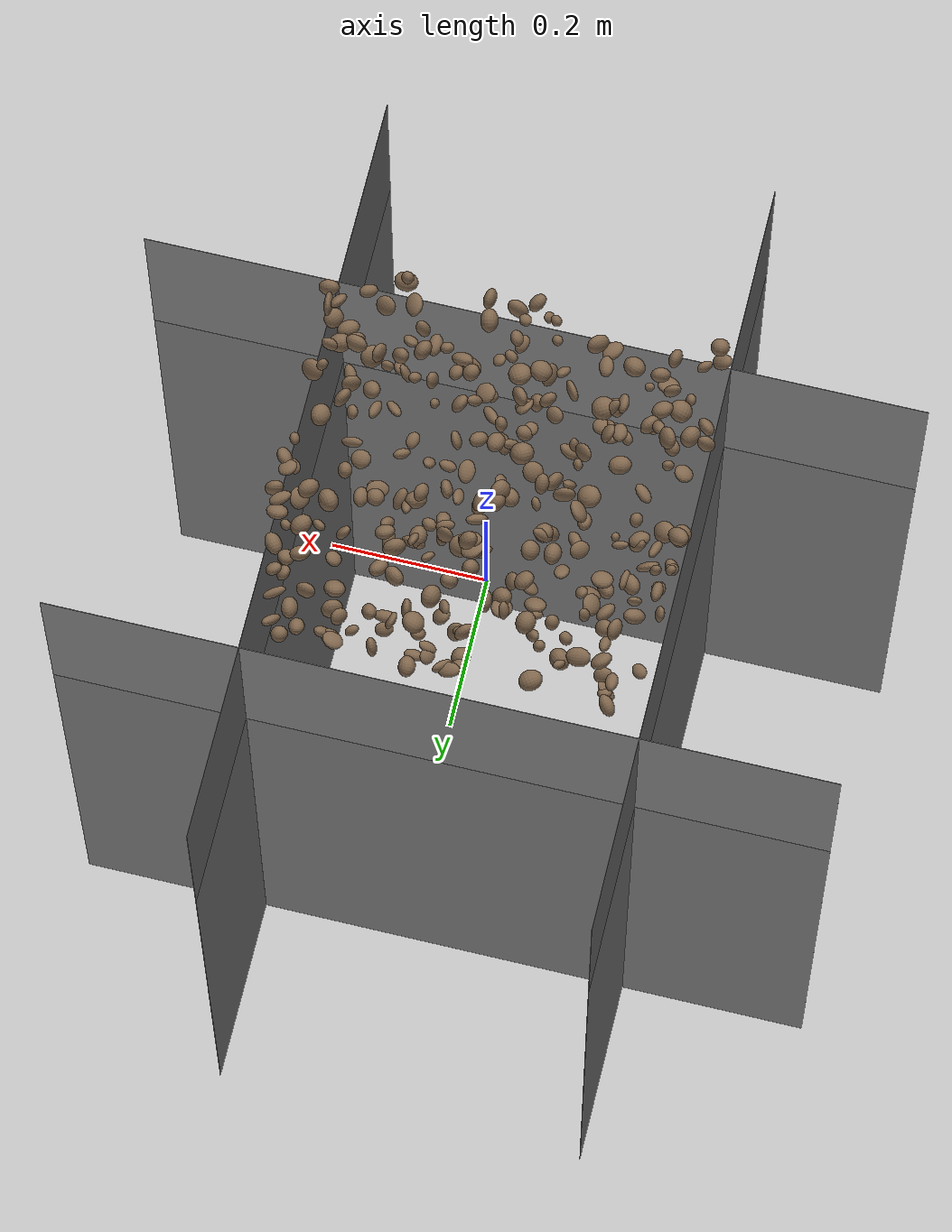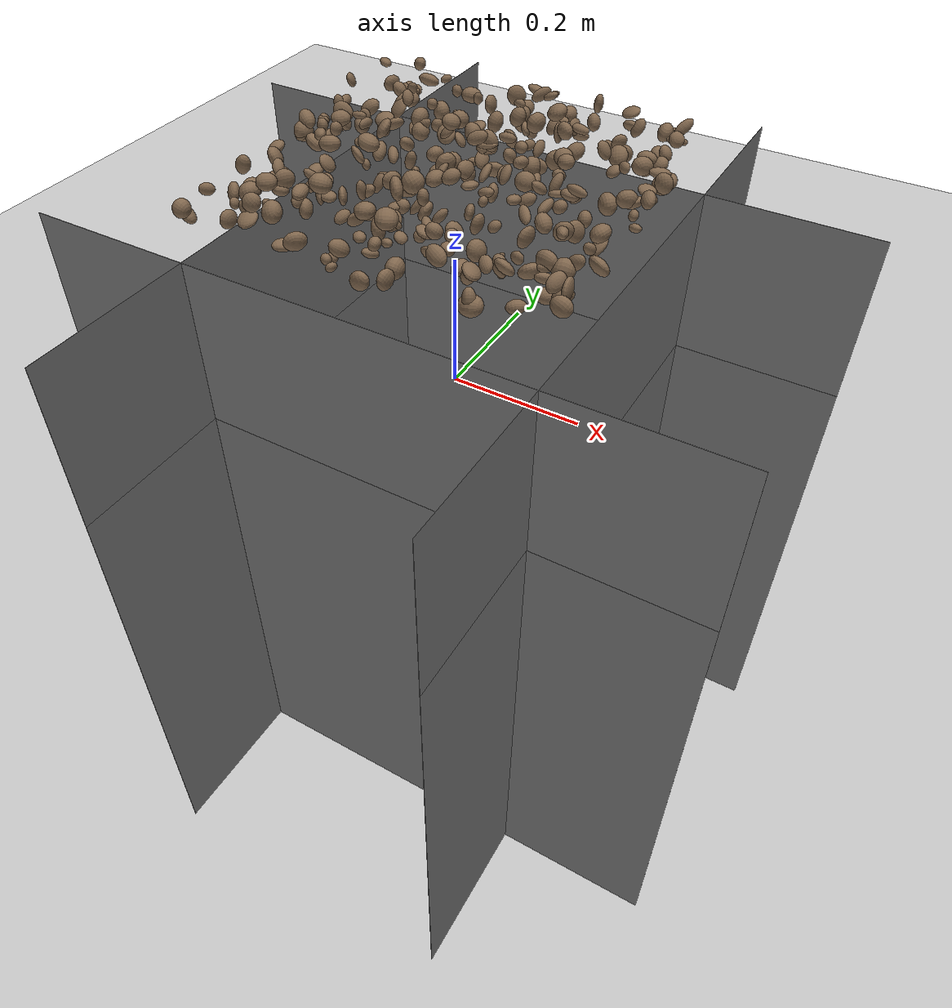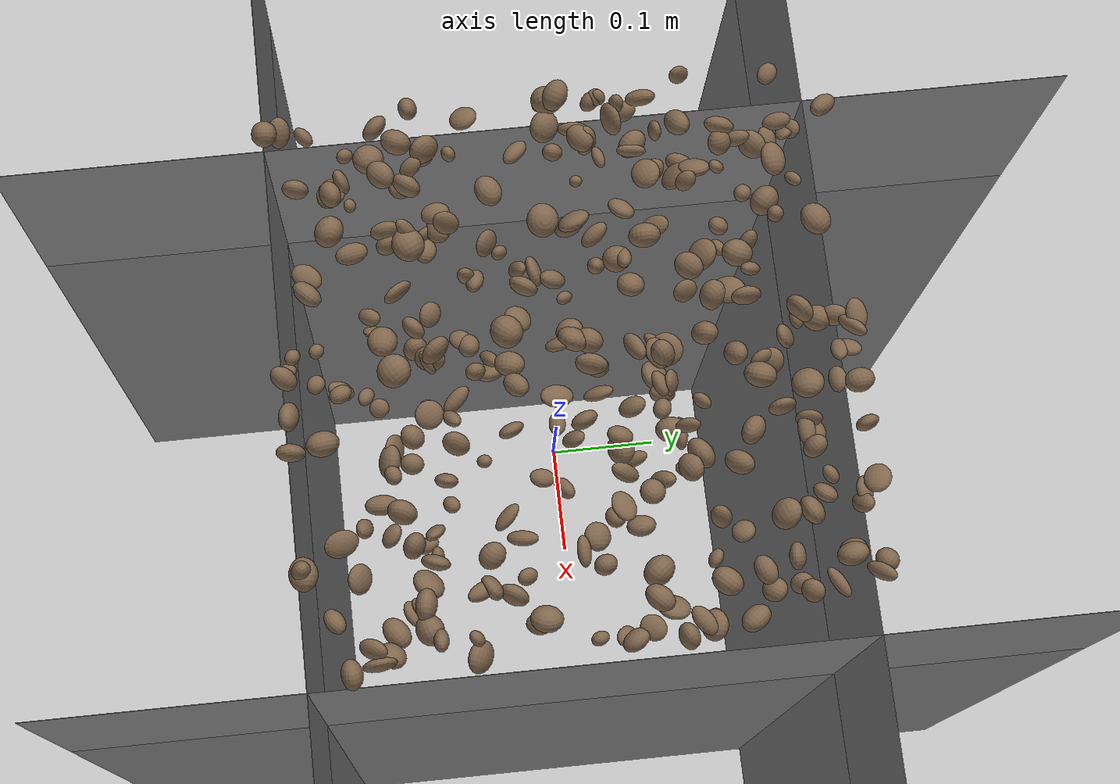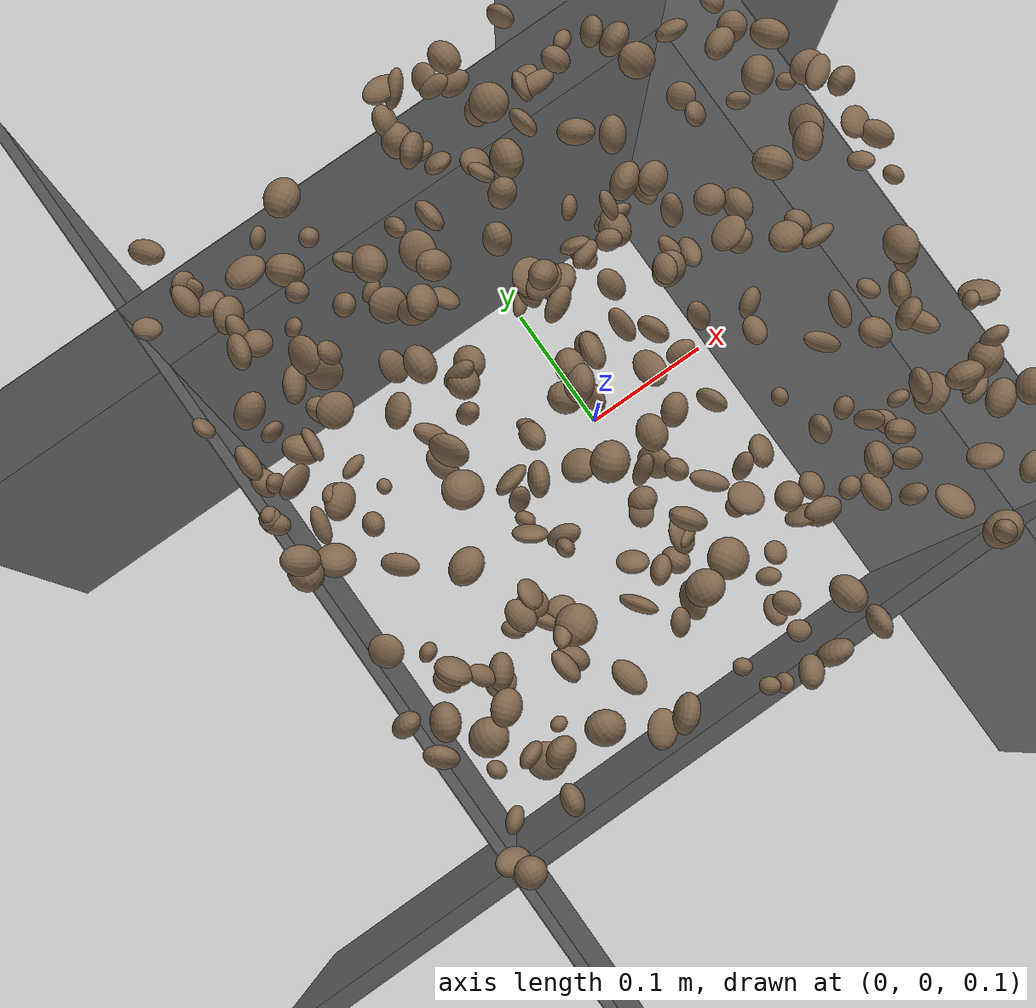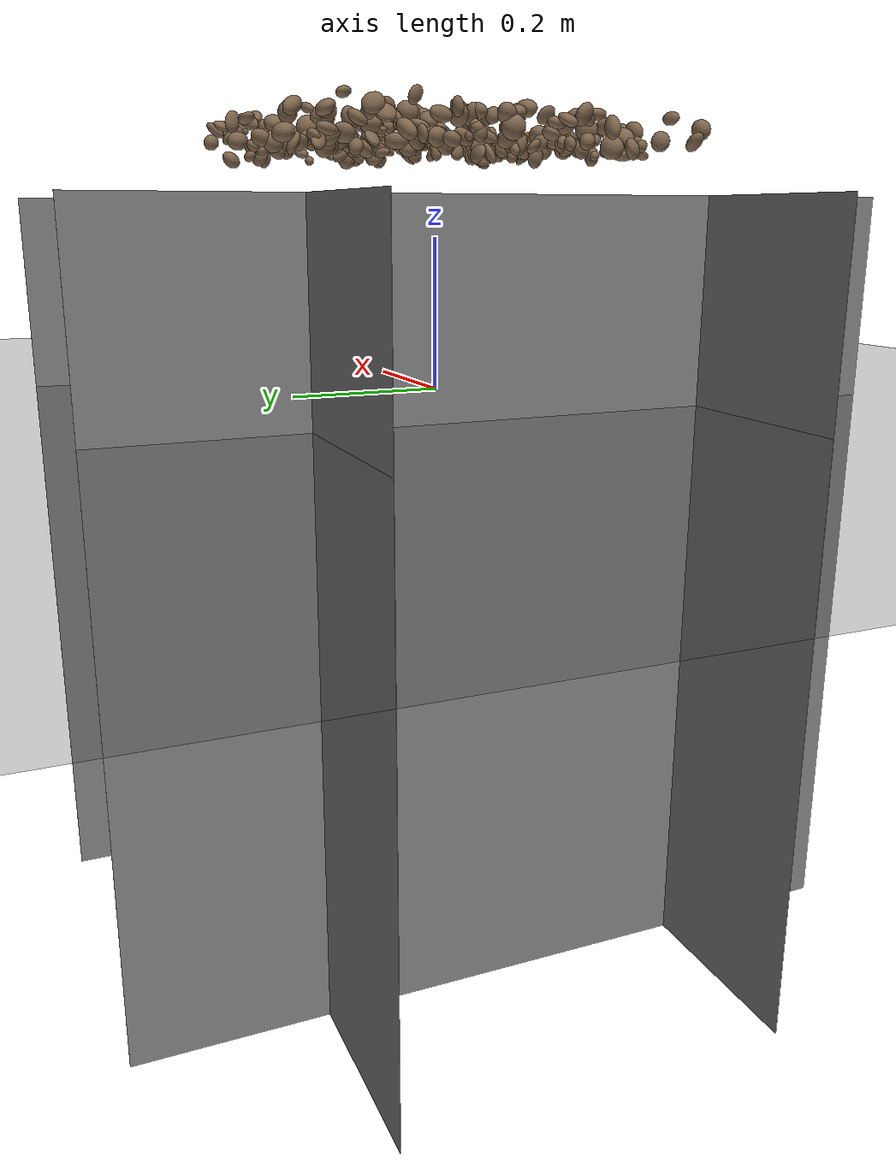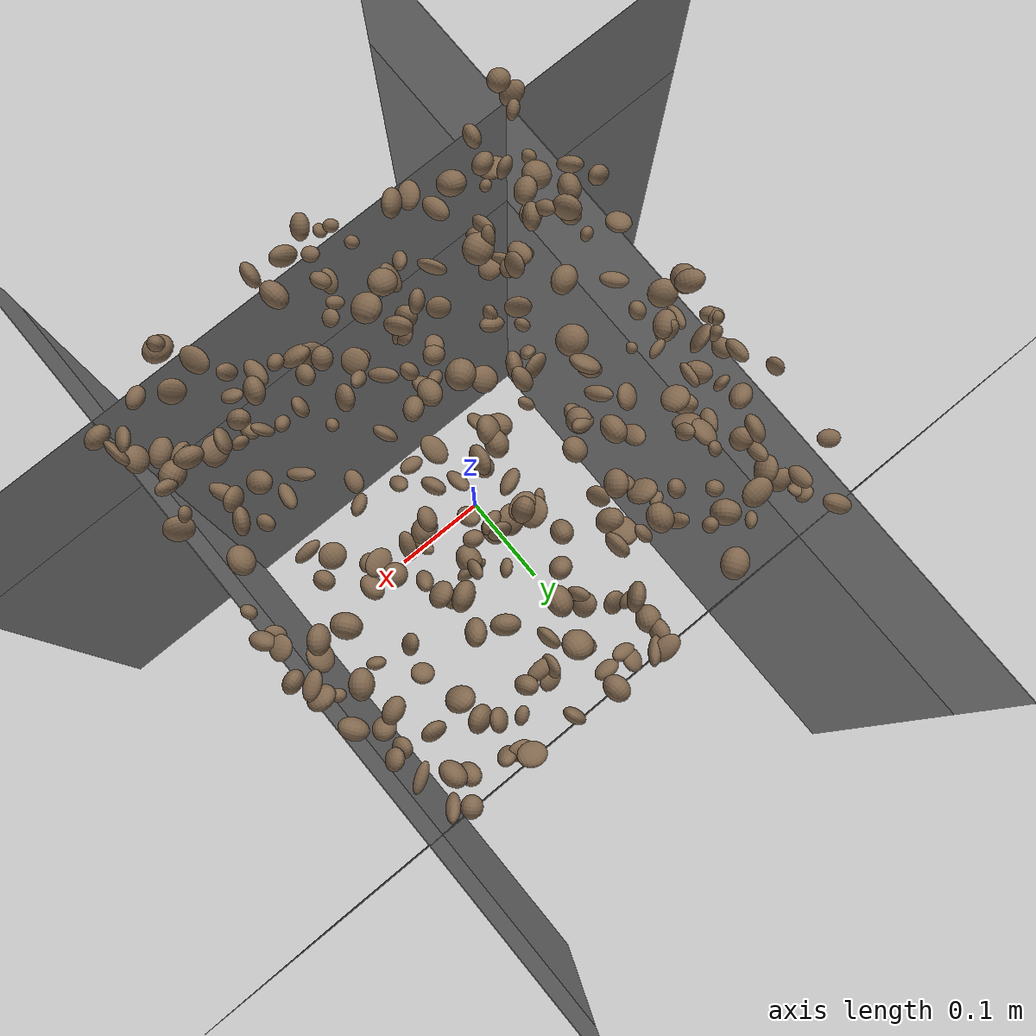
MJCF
<mujoco model="rocky_terrain_scene">

  <default>
    <default class="wall">
      <geom type="plane" size=".5 .5 .05" />
    </default>
  </default>

    <compiler angle="radian" inertiafromgeom="true" />
    <option timestep="0.002" gravity="0 0 -9.81" />

    <worldbody>

        <geom name="+x" class="wall" zaxis="1 0 0" pos="-.25 0 -.25" />
        <geom name="-x" class="wall" zaxis="-1 0 0" pos=".25 0 -.25" />
        <geom name="+y" class="wall" zaxis="0 1 0" pos="0 -.25 -.25" />
        <geom name="-y" class="wall" zaxis="0 -1 0" pos="0 .25 -.25" />

        <light name="sunlight" pos="5 5 5" dir="-1 -1 -1" diffuse="1 1 1" specular="0.5 0.5 0.5" ambient="0.5 0.5 0.5" />

        <geom name="ground_plane" type="plane" size="50 50 0.1" rgba="0.3 0.3 0.3 1" />

        <body name="rocky_terrain_body">

        </body>
    <body name="rock1" pos="0.23514635536224038 -0.17241597106223705 0.3182748317262511"><joint type="free" /><geom type="ellipsoid" size="0.012786552052019213 0.008751085456726692 0.012572126742247947" quat="0.4850396396795264 0.17979970620020833 0.1011137232680894 0.23404693085217587" rgba="0.5 0.4 0.3 1" /><inertial pos="0.23514635536224038 -0.17241597106223705 0.3182748317262511" quat="0.4850396396795264 0.17979970620020833 0.1011137232680894 0.23404693085217587" mass="1.6163883858813657e-05" /></body><body name="rock2" pos="0.02148466937231841 -0.046619142904563315 0.345705972628241"><joint type="free" /><geom type="ellipsoid" size="0.012354919998662329 0.009455006373318042 0.008927985967333242" quat="0.4458374277800801 0.2992832611386394 0.010040735038460155 0.24483857604282036" rgba="0.5 0.4 0.3 1" /><inertial pos="0.02148466937231841 -0.046619142904563315 0.345705972628241" quat="0.4458374277800801 0.2992832611386394 0.010040735038460155 0.24483857604282036" mass="1.073282631864271e-05" /></body><body name="rock3" pos="0.035665168795391444 0.07780346830104196 0.3244243067911686"><joint type="free" /><geom type="ellipsoid" size="0.013247695594464964 0.00911308126732017 0.007866568766788498" quat="0.38781386128483397 0.08435656008305556 0.30940142606037463 0.21842815257173584" rgba="0.5 0.4 0.3 1" /><inertial pos="0.035665168795391444 0.07780346830104196 0.3244243067911686" quat="0.38781386128483397 0.08435656008305556 0.30940142606037463 0.21842815257173584" mass="5.8677100090691195e-05" /></body><body name="rock4" pos="-0.05126700528714612 0.13383596537561615 0.3133215180813706"><joint type="free" /><geom type="ellipsoid" size="0.011309820477832407 0.014281635242846345 0.011360664163397073" quat="0.43097365335557214 0.2627633081275312 0.07050171956676282 0.2357613189501338" rgba="0.5 0.4 0.3 1" /><inertial pos="-0.05126700528714612 0.13383596537561615 0.3133215180813706" quat="0.43097365335557214 0.2627633081275312 0.07050171956676282 0.2357613189501338" mass="7.885016258745627e-05" /></body><body name="rock5" pos="0.19724337999794556 -0.06653006414807439 0.33214493424570124"><joint type="free" /><geom type="ellipsoid" size="0.012442955308628111 0.014254808840995243 0.007439313036926749" quat="0.2800221885197236 0.3327016630411832 0.09526354316260605 0.29201260527648704" rgba="0.5 0.4 0.3 1" /><inertial pos="0.19724337999794556 -0.06653006414807439 0.33214493424570124" quat="0.2800221885197236 0.3327016630411832 0.09526354316260605 0.29201260527648704" mass="7.182108469533336e-05" /></body><body name="rock6" pos="0.034504591300713705 0.23142140340701145 0.3109157619132989"><joint type="free" /><geom type="ellipsoid" size="0.0064156000620899135 0.008179160482856072 0.011858925348074435" quat="0.4091652379241539 0.10473849518929969 0.3554290136002845 0.13066725328626194" rgba="0.5 0.4 0.3 1" /><inertial pos="0.034504591300713705 0.23142140340701145 0.3109157619132989" quat="0.4091652379241539 0.10473849518929969 0.3554290136002845 0.13066725328626194" mass="7.577040395646603e-05" /></body><body name="rock7" pos="-0.13683578986534273 0.1923446513236352 0.3033896321250264"><joint type="free" /><geom type="ellipsoid" size="0.014001761412560699 0.014104195031623641 0.01160929444407004" quat="0.07931278959760368 0.21155149882357427 0.30936691742541234 0.3997687941534096" rgba="0.5 0.4 0.3 1" /><inertial pos="-0.13683578986534273 0.1923446513236352 0.3033896321250264" quat="0.07931278959760368 0.21155149882357427 0.30936691742541234 0.3997687941534096" mass="5.172666910146063e-05" /></body><body name="rock8" pos="0.05628832267986161 0.1790344677687134 0.32033453759763475"><joint type="free" /><geom type="ellipsoid" size="0.006118829923343034 0.014226092800545657 0.01214523817099639" quat="0.4138759997281464 0.5008836912180099 0.03471327985618741 0.05052702919765621" rgba="0.5 0.4 0.3 1" /><inertial pos="0.05628832267986161 0.1790344677687134 0.32033453759763475" quat="0.4138759997281464 0.5008836912180099 0.03471327985618741 0.05052702919765621" mass="7.476575560295875e-05" /></body><body name="rock9" pos="0.09886174328547626 0.03912066371712397 0.3135205327993495"><joint type="free" /><geom type="ellipsoid" size="0.014915904894969998 0.006739426129327502 0.0077664990218278065" quat="0.3267494666402836 0.30921589765272867 0.34149694897332555 0.022537686733662233" rgba="0.5 0.4 0.3 1" /><inertial pos="0.09886174328547626 0.03912066371712397 0.3135205327993495" quat="0.3267494666402836 0.30921589765272867 0.34149694897332555 0.022537686733662233" mass="4.673358878812191e-05" /></body><body name="rock10" pos="-0.22497518945587203 -0.1281586959742646 0.3029834477174657"><joint type="free" /><geom type="ellipsoid" size="0.01088129550044845 0.01386878576159431 0.013924854187514862" quat="0.09469085057725812 0.10994653555826642 0.3003997989822376 0.4949628148822378" rgba="0.5 0.4 0.3 1" /><inertial pos="-0.22497518945587203 -0.1281586959742646 0.3029834477174657" quat="0.09469085057725812 0.10994653555826642 0.3003997989822376 0.4949628148822378" mass="1.6487378614700433e-05" /></body><body name="rock11" pos="-0.24135001596209288 -0.23093620564749473 0.3102077287712784"><joint type="free" /><geom type="ellipsoid" size="0.007502582543320846 0.01009780922964363 0.014131000000475204" quat="0.06201088012746342 0.5911398254679672 0.05957183029447812 0.28727746411009136" rgba="0.5 0.4 0.3 1" /><inertial pos="-0.24135001596209288 -0.23093620564749473 0.3102077287712784" quat="0.06201088012746342 0.5911398254679672 0.05957183029447812 0.28727746411009136" mass="5.175680946645954e-05" /></body><body name="rock12" pos="0.023333050582301562 -0.12256663374450377 0.30350447546812204"><joint type="free" /><geom type="ellipsoid" size="0.007646435156597714 0.00807867609819187 0.007714877552393758" quat="0.3060497797947889 0.08579266486402261 0.21202458191252088 0.39613297342866755" rgba="0.5 0.4 0.3 1" /><inertial pos="0.023333050582301562 -0.12256663374450377 0.30350447546812204" quat="0.3060497797947889 0.08579266486402261 0.21202458191252088 0.39613297342866755" mass="7.65304204858889e-05" /></body><body name="rock13" pos="-0.18745934699536865 0.17031702660567588 0.3296113932092467"><joint type="free" /><geom type="ellipsoid" size="0.006834356592523271 0.01274866753875379 0.0071078910736190794" quat="0.18576460882387197 0.059385253123327555 0.5918679175980764 0.162982220454724" rgba="0.5 0.4 0.3 1" /><inertial pos="-0.18745934699536865 0.17031702660567588 0.3296113932092467" quat="0.18576460882387197 0.059385253123327555 0.5918679175980764 0.162982220454724" mass="1.2907724378206309e-05" /></body><body name="rock14" pos="-0.18882189949752204 -0.025614232212541665 0.34240722082555214"><joint type="free" /><geom type="ellipsoid" size="0.008227153788816962 0.006472765206455015 0.013380444506777101" quat="0.32680824178071827 0.3590993888621864 0.03696071478354299 0.2771316545735524" rgba="0.5 0.4 0.3 1" /><inertial pos="-0.18882189949752204 -0.025614232212541665 0.34240722082555214" quat="0.32680824178071827 0.3590993888621864 0.03696071478354299 0.2771316545735524" mass="1.2015424700866678e-05" /></body><body name="rock15" pos="-0.01497561337423825 -0.06516572338739873 0.3064751102608981"><joint type="free" /><geom type="ellipsoid" size="0.006273893523427238 0.014849196038497624 0.0058923516220899886" quat="0.19546461075754937 0.26921684701554355 0.39650463303192185 0.1388139091949854" rgba="0.5 0.4 0.3 1" /><inertial pos="-0.01497561337423825 -0.06516572338739873 0.3064751102608981" quat="0.19546461075754937 0.26921684701554355 0.39650463303192185 0.1388139091949854" mass="3.9043934666093835e-05" /></body><body name="rock16" pos="0.0007538603626038309 -0.050100825037393104 0.3398066345593269"><joint type="free" /><geom type="ellipsoid" size="0.013260765918233785 0.009715482210313773 0.010775568178474203" quat="0.30761285997681076 0.2703047514685724 0.1533269210877442 0.2687554674668727" rgba="0.5 0.4 0.3 1" /><inertial pos="0.0007538603626038309 -0.050100825037393104 0.3398066345593269" quat="0.30761285997681076 0.2703047514685724 0.1533269210877442 0.2687554674668727" mass="5.298490790647464e-05" /></body><body name="rock17" pos="-0.07338900585423686 -0.1389732418159012 0.3370563999862118"><joint type="free" /><geom type="ellipsoid" size="0.014092850912137845 0.011073278146656637 0.005362065200629555" quat="0.20687108980344274 0.13688905491447756 0.34141124316492516 0.3148286121171545" rgba="0.5 0.4 0.3 1" /><inertial pos="-0.07338900585423686 -0.1389732418159012 0.3370563999862118" quat="0.20687108980344274 0.13688905491447756 0.34141124316492516 0.3148286121171545" mass="9.041451356995289e-05" /></body><body name="rock18" pos="0.08874661244916332 0.0472170239933935 0.31547317818174053"><joint type="free" /><geom type="ellipsoid" size="0.013079933306884874 0.005876767874700128 0.006318042858371795" quat="0.07211878169062397 0.3448965654820462 0.3054442942117402 0.27754035861558946" rgba="0.5 0.4 0.3 1" /><inertial pos="0.08874661244916332 0.0472170239933935 0.31547317818174053" quat="0.07211878169062397 0.3448965654820462 0.3054442942117402 0.27754035861558946" mass="7.617430049771877e-05" /></body><body name="rock19" pos="-0.1952609286985414 0.15471217345092336 0.34422684408783133"><joint type="free" /><geom type="ellipsoid" size="0.007619627564647101 0.013568269253323034 0.011537186201835248" quat="0.07631993525173038 0.11401427619018809 0.13905393261526508 0.6706118559428164" rgba="0.5 0.4 0.3 1" /><inertial pos="-0.1952609286985414 0.15471217345092336 0.34422684408783133" quat="0.07631993525173038 0.11401427619018809 0.13905393261526508 0.6706118559428164" mass="3.873322829162971e-05" /></body><body name="rock20" pos="0.011158839346774141 -0.17433306428475298 0.31705340933787735"><joint type="free" /><geom type="ellipsoid" size="0.006473992441324192 0.005655523333446433 0.008817519595146726" quat="0.42280258172435714 0.2373309987052217 0.1852112500401167 0.15465516953030434" rgba="0.5 0.4 0.3 1" /><inertial pos="0.011158839346774141 -0.17433306428475298 0.31705340933787735" quat="0.42280258172435714 0.2373309987052217 0.1852112500401167 0.15465516953030434" mass="5.664161806284036e-05" /></body><body name="rock21" pos="0.20972127512591904 0.05476566440938618 0.3207178870209901"><joint type="free" /><geom type="ellipsoid" size="0.013966400202825125 0.012301969227467562 0.010080995855289522" quat="0.3200401070660848 0.38387367805867184 0.19653351452339585 0.09955270035184748" rgba="0.5 0.4 0.3 1" /><inertial pos="0.20972127512591904 0.05476566440938618 0.3207178870209901" quat="0.3200401070660848 0.38387367805867184 0.19653351452339585 0.09955270035184748" mass="6.306270666547638e-05" /></body><body name="rock22" pos="0.030096851128890767 0.16170785652858605 0.33478191810136926"><joint type="free" /><geom type="ellipsoid" size="0.014036653852424228 0.01452801473983293 0.010948334733650856" quat="0.16832103252933542 0.44433286120714155 0.09752571015083804 0.28982039611268506" rgba="0.5 0.4 0.3 1" /><inertial pos="0.030096851128890767 0.16170785652858605 0.33478191810136926" quat="0.16832103252933542 0.44433286120714155 0.09752571015083804 0.28982039611268506" mass="9.01712764526136e-05" /></body><body name="rock23" pos="-0.11706549525177484 -0.11155422059807646 0.31249779469413835"><joint type="free" /><geom type="ellipsoid" size="0.010055109166283556 0.0066399926695299046 0.011084546240053412" quat="0.2641712832062343 0.266369088155437 0.24173483679467941 0.22772479184364933" rgba="0.5 0.4 0.3 1" /><inertial pos="-0.11706549525177484 -0.11155422059807646 0.31249779469413835" quat="0.2641712832062343 0.266369088155437 0.24173483679467941 0.22772479184364933" mass="1.816733873349748e-05" /></body><body name="rock24" pos="-0.24232702098271125 0.055108780221015785 0.3202104441640308"><joint type="free" /><geom type="ellipsoid" size="0.006230352368315619 0.007925996630992313 0.0059969232765153535" quat="0.33446198035347047 0.3522480344098372 0.056714410747576084 0.25657557448911616" rgba="0.5 0.4 0.3 1" /><inertial pos="-0.24232702098271125 0.055108780221015785 0.3202104441640308" quat="0.33446198035347047 0.3522480344098372 0.056714410747576084 0.25657557448911616" mass="3.293889557131839e-05" /></body><body name="rock25" pos="0.14789505361654365 0.17099970030900125 0.3130441202205985"><joint type="free" /><geom type="ellipsoid" size="0.009779839270151478 0.014736349709225344 0.012855763788147099" quat="0.3749366662519953 0.08411033711104829 0.32520222628752044 0.2157507703494359" rgba="0.5 0.4 0.3 1" /><inertial pos="0.14789505361654365 0.17099970030900125 0.3130441202205985" quat="0.3749366662519953 0.08411033711104829 0.32520222628752044 0.2157507703494359" mass="3.444123836806071e-05" /></body><body name="rock26" pos="0.181841518289653 -0.053526079710433994 0.3253485519167678"><joint type="free" /><geom type="ellipsoid" size="0.008771597872839829 0.0061278618244443 0.007840686475101138" quat="0.1854017826441559 0.30522096519691433 0.43407642901179155 0.07530082314713821" rgba="0.5 0.4 0.3 1" /><inertial pos="0.181841518289653 -0.053526079710433994 0.3253485519167678" quat="0.1854017826441559 0.30522096519691433 0.43407642901179155 0.07530082314713821" mass="7.910220688081116e-05" /></body><body name="rock27" pos="0.16945715416222712 -0.005897060305514512 0.3478248380493365"><joint type="free" /><geom type="ellipsoid" size="0.005823180824759264 0.006848890032180262 0.013445374840701033" quat="0.17918911551388425 0.3245865939907341 0.23822199700862126 0.25800229348676046" rgba="0.5 0.4 0.3 1" /><inertial pos="0.16945715416222712 -0.005897060305514512 0.3478248380493365" quat="0.17918911551388425 0.3245865939907341 0.23822199700862126 0.25800229348676046" mass="1.724793831103964e-05" /></body><body name="rock28" pos="-0.17078134577748705 0.09446135674190032 0.31050369243326875"><joint type="free" /><geom type="ellipsoid" size="0.014324754815358737 0.010658353245149342 0.009239664068010762" quat="0.058755124178421554 0.2887595431346913 0.24595820817277797 0.4065271245141092" rgba="0.5 0.4 0.3 1" /><inertial pos="-0.17078134577748705 0.09446135674190032 0.31050369243326875" quat="0.058755124178421554 0.2887595431346913 0.24595820817277797 0.4065271245141092" mass="1.0419798433774963e-05" /></body><body name="rock29" pos="-0.1965240138922782 0.037542038369170916 0.3353343453959138"><joint type="free" /><geom type="ellipsoid" size="0.009397894072479176 0.014665058956250792 0.00808407744416383" quat="0.31376714812607304 0.15491138578013763 0.2092099876848293 0.32211147840896004" rgba="0.5 0.4 0.3 1" /><inertial pos="-0.1965240138922782 0.037542038369170916 0.3353343453959138" quat="0.31376714812607304 0.15491138578013763 0.2092099876848293 0.32211147840896004" mass="1.865071278950726e-05" /></body><body name="rock30" pos="0.23625273832022464 0.024151281805641356 0.30388412915464125"><joint type="free" /><geom type="ellipsoid" size="0.007667881327736575 0.005430746043488383 0.009973977142356184" quat="0.48385122023741695 0.2690210172960592 0.15760663512385906 0.08952112734266476" rgba="0.5 0.4 0.3 1" /><inertial pos="0.23625273832022464 0.024151281805641356 0.30388412915464125" quat="0.48385122023741695 0.2690210172960592 0.15760663512385906 0.08952112734266476" mass="4.5844319978022286e-05" /></body><body name="rock31" pos="0.002557318634350325 -0.19547352422439362 0.31200598929860424"><joint type="free" /><geom type="ellipsoid" size="0.012009748905370935 0.005919701326944683 0.00800674857805152" quat="0.35275931513031095 0.23484309215642243 0.2636444608154111 0.1487531318978554" rgba="0.5 0.4 0.3 1" /><inertial pos="0.002557318634350325 -0.19547352422439362 0.31200598929860424" quat="0.35275931513031095 0.23484309215642243 0.2636444608154111 0.1487531318978554" mass="5.334458915563915e-05" /></body><body name="rock32" pos="0.001371407686502124 -0.07931059561059944 0.3283283389089654"><joint type="free" /><geom type="ellipsoid" size="0.008566814339968452 0.01130546187507581 0.007305425977640343" quat="0.1795415527833898 0.24361275938163549 0.27662118099117317 0.3002245068438015" rgba="0.5 0.4 0.3 1" /><inertial pos="0.001371407686502124 -0.07931059561059944 0.3283283389089654" quat="0.1795415527833898 0.24361275938163549 0.27662118099117317 0.3002245068438015" mass="8.222391385955708e-05" /></body><body name="rock33" pos="-0.018477362359548777 0.006936803091923294 0.33035939859523855"><joint type="free" /><geom type="ellipsoid" size="0.014017340990425804 0.009931062284189432 0.01483115711174086" quat="0.542393980113169 0.09690198232109935 0.045298330297600095 0.31540570726813166" rgba="0.5 0.4 0.3 1" /><inertial pos="-0.018477362359548777 0.006936803091923294 0.33035939859523855" quat="0.542393980113169 0.09690198232109935 0.045298330297600095 0.31540570726813166" mass="5.3408160071642465e-05" /></body><body name="rock34" pos="0.07924878260769919 0.19580012613725 0.32470587684383584"><joint type="free" /><geom type="ellipsoid" size="0.007486374483481342 0.005923737114012683 0.014175149709736802" quat="0.22132701974586738 0.2774324947230829 0.25962373187886373 0.24161675365218596" rgba="0.5 0.4 0.3 1" /><inertial pos="0.07924878260769919 0.19580012613725 0.32470587684383584" quat="0.22132701974586738 0.2774324947230829 0.25962373187886373 0.24161675365218596" mass="6.76259967292414e-05" /></body><body name="rock35" pos="-0.03770628000938825 -0.21412774104957277 0.30357093193986784"><joint type="free" /><geom type="ellipsoid" size="0.0069498860360388565 0.006445613394189195 0.006110466008833946" quat="0.19792836551718387 0.09930171014184452 0.3090435272602586 0.3937263970807131" rgba="0.5 0.4 0.3 1" /><inertial pos="-0.03770628000938825 -0.21412774104957277 0.30357093193986784" quat="0.19792836551718387 0.09930171014184452 0.3090435272602586 0.3937263970807131" mass="2.3551685627222083e-05" /></body><body name="rock36" pos="0.197283321163211 0.24739026317958962 0.322945892983218"><joint type="free" /><geom type="ellipsoid" size="0.009694172626871281 0.010158594281255756 0.010386780992159509" quat="0.05916818373203956 0.24905934151163547 0.3746174259014605 0.3171550488548644" rgba="0.5 0.4 0.3 1" /><inertial pos="0.197283321163211 0.24739026317958962 0.322945892983218" quat="0.05916818373203956 0.24905934151163547 0.3746174259014605 0.3171550488548644" mass="1.0608582118054647e-05" /></body><body name="rock37" pos="-0.1004874149118869 0.07739141954969048 0.3452982826082851"><joint type="free" /><geom type="ellipsoid" size="0.012195620275906954 0.01394118485935213 0.010568631339000623" quat="0.4292145816261553 0.06427944195143731 0.4601758744594922 0.04633010196291523" rgba="0.5 0.4 0.3 1" /><inertial pos="-0.1004874149118869 0.07739141954969048 0.3452982826082851" quat="0.4292145816261553 0.06427944195143731 0.4601758744594922 0.04633010196291523" mass="3.226736839631225e-05" /></body><body name="rock38" pos="-0.2369472380644742 0.2021326730411374 0.3498332229180767"><joint type="free" /><geom type="ellipsoid" size="0.010248201542604397 0.005602847150078126 0.008132436105878434" quat="0.09697395400836947 0.1615372944247459 0.4289591362878275 0.31252961527905715" rgba="0.5 0.4 0.3 1" /><inertial pos="-0.2369472380644742 0.2021326730411374 0.3498332229180767" quat="0.09697395400836947 0.1615372944247459 0.4289591362878275 0.31252961527905715" mass="2.108753036451676e-05" /></body><body name="rock39" pos="0.24911312039792805 -0.20620252848128284 0.3292520947548388"><joint type="free" /><geom type="ellipsoid" size="0.009227669628876091 0.012059432362241782 0.0132464662896889" quat="0.18407992929956282 0.2935289035297311 0.33676825681367706 0.185622910357029" rgba="0.5 0.4 0.3 1" /><inertial pos="0.24911312039792805 -0.20620252848128284 0.3292520947548388" quat="0.18407992929956282 0.2935289035297311 0.33676825681367706 0.185622910357029" mass="7.860094543851858e-05" /></body><body name="rock40" pos="0.21534071821675693 -0.16672384634698995 0.3090812522265469"><joint type="free" /><geom type="ellipsoid" size="0.014378040732457357 0.00980446942018355 0.010354971164520083" quat="0.3815943826426539 0.3763820438481737 0.1277425176856427 0.11428105582352983" rgba="0.5 0.4 0.3 1" /><inertial pos="0.21534071821675693 -0.16672384634698995 0.3090812522265469" quat="0.3815943826426539 0.3763820438481737 0.1277425176856427 0.11428105582352983" mass="9.857872780114535e-05" /></body><body name="rock41" pos="0.06945007563869876 0.0902042726492473 0.31264136472654813"><joint type="free" /><geom type="ellipsoid" size="0.006174359028399243 0.011173021767316858 0.01480607162158749" quat="0.2902036704122289 0.21881908784443196 0.21877507642202537 0.2722021653213138" rgba="0.5 0.4 0.3 1" /><inertial pos="0.06945007563869876 0.0902042726492473 0.31264136472654813" quat="0.2902036704122289 0.21881908784443196 0.21877507642202537 0.2722021653213138" mass="7.457535567878934e-05" /></body><body name="rock42" pos="0.18371594066113822 0.10340397242036536 0.3343078454734584"><joint type="free" /><geom type="ellipsoid" size="0.005572740110435923 0.007664768481032702 0.008572031741174303" quat="0.32873749331776003 0.30553415189171623 0.23620692529095724 0.12952142949956647" rgba="0.5 0.4 0.3 1" /><inertial pos="0.18371594066113822 0.10340397242036536 0.3343078454734584" quat="0.32873749331776003 0.30553415189171623 0.23620692529095724 0.12952142949956647" mass="9.995244869091923e-05" /></body><body name="rock43" pos="0.22688919732901885 0.10050093665610865 0.30295824570388064"><joint type="free" /><geom type="ellipsoid" size="0.006074266052874998 0.006418646921074289 0.007131548019700028" quat="0.4212384980783785 0.24065021916058943 0.1999241145980116 0.1381871681630205" rgba="0.5 0.4 0.3 1" /><inertial pos="0.22688919732901885 0.10050093665610865 0.30295824570388064" quat="0.4212384980783785 0.24065021916058943 0.1999241145980116 0.1381871681630205" mass="3.0476579646582934e-05" /></body><body name="rock44" pos="0.10591976184298274 -0.16949002911193373 0.3115720659007499"><joint type="free" /><geom type="ellipsoid" size="0.014501589558592026 0.0086013588052579 0.00866333141824627" quat="0.15086705935124947 0.3506172005148285 0.34851342112442485 0.1500023190094973" rgba="0.5 0.4 0.3 1" /><inertial pos="0.10591976184298274 -0.16949002911193373 0.3115720659007499" quat="0.15086705935124947 0.3506172005148285 0.34851342112442485 0.1500023190094973" mass="3.7549911385662633e-05" /></body><body name="rock45" pos="0.009308467839766577 -0.1957766004730001 0.32618732369230596"><joint type="free" /><geom type="ellipsoid" size="0.01019259577995478 0.008830261871141616 0.00744395823956351" quat="0.17837055743645794 0.21085036572425345 0.42790546815572705 0.18287360868356153" rgba="0.5 0.4 0.3 1" /><inertial pos="0.009308467839766577 -0.1957766004730001 0.32618732369230596" quat="0.17837055743645794 0.21085036572425345 0.42790546815572705 0.18287360868356153" mass="5.633314411553332e-05" /></body><body name="rock46" pos="0.2340051109676236 0.13267572234230796 0.31595437514756525"><joint type="free" /><geom type="ellipsoid" size="0.009846441268183643 0.011023794290957727 0.014011278100525198" quat="0.4611975761908397 0.30633398625387936 0.19462169281309075 0.03784674474219027" rgba="0.5 0.4 0.3 1" /><inertial pos="0.2340051109676236 0.13267572234230796 0.31595437514756525" quat="0.4611975761908397 0.30633398625387936 0.19462169281309075 0.03784674474219027" mass="5.6698123258341235e-05" /></body><body name="rock47" pos="-0.08340602676113279 0.051560990435218446 0.33994449132823584"><joint type="free" /><geom type="ellipsoid" size="0.01224124975668441 0.011798380717740187 0.010947995107243418" quat="0.2761338226601625 0.244319650413363 0.11038558510000576 0.36916094182646875" rgba="0.5 0.4 0.3 1" /><inertial pos="-0.08340602676113279 0.051560990435218446 0.33994449132823584" quat="0.2761338226601625 0.244319650413363 0.11038558510000576 0.36916094182646875" mass="9.869836384774623e-05" /></body><body name="rock48" pos="-0.07742522095486792 -0.02914651059622897 0.3080482771372497"><joint type="free" /><geom type="ellipsoid" size="0.013209433501404196 0.012513219609686325 0.00754407342555216" quat="0.3118264482490676 0.32017765264563697 0.2077305139535228 0.1602653851517726" rgba="0.5 0.4 0.3 1" /><inertial pos="-0.07742522095486792 -0.02914651059622897 0.3080482771372497" quat="0.3118264482490676 0.32017765264563697 0.2077305139535228 0.1602653851517726" mass="5.2919995215244626e-05" /></body><body name="rock49" pos="-0.016048532559043538 -0.005636965885513434 0.3272374017407941"><joint type="free" /><geom type="ellipsoid" size="0.013180603269587868 0.005149378772911403 0.008467993561386404" quat="0.32296928138114883 0.27056587175169444 0.020825752251151616 0.3856390946160051" rgba="0.5 0.4 0.3 1" /><inertial pos="-0.016048532559043538 -0.005636965885513434 0.3272374017407941" quat="0.32296928138114883 0.27056587175169444 0.020825752251151616 0.3856390946160051" mass="7.760957878893258e-05" /></body><body name="rock50" pos="-0.16084727010573407 0.1981301677769839 0.3410541278001603"><joint type="free" /><geom type="ellipsoid" size="0.008037145434953437 0.011930315268575211 0.01496780526495332" quat="0.09304803397549956 0.4086567837787439 0.12117362397764009 0.3771215582681164" rgba="0.5 0.4 0.3 1" /><inertial pos="-0.16084727010573407 0.1981301677769839 0.3410541278001603" quat="0.09304803397549956 0.4086567837787439 0.12117362397764009 0.3771215582681164" mass="3.487300768647297e-05" /></body><body name="rock51" pos="0.10036631207943125 -0.03244964163860242 0.3300706389084487"><joint type="free" /><geom type="ellipsoid" size="0.006257256852122854 0.010853914344021637 0.007888321779473212" quat="0.0904973910094326 0.44399481133753554 0.0008159467268281408 0.46469185092620374" rgba="0.5 0.4 0.3 1" /><inertial pos="0.10036631207943125 -0.03244964163860242 0.3300706389084487" quat="0.0904973910094326 0.44399481133753554 0.0008159467268281408 0.46469185092620374" mass="6.834752415069483e-05" /></body><body name="rock52" pos="0.10437730807999795 0.09289390872008313 0.3332579268882019"><joint type="free" /><geom type="ellipsoid" size="0.011438814477796332 0.008431576422006214 0.012207688832481077" quat="0.04854323937756469 0.3167661144149236 0.23306443579417602 0.4016262104133357" rgba="0.5 0.4 0.3 1" /><inertial pos="0.10437730807999795 0.09289390872008313 0.3332579268882019" quat="0.04854323937756469 0.3167661144149236 0.23306443579417602 0.4016262104133357" mass="2.307481804814879e-05" /></body><body name="rock53" pos="-0.1923125045405284 0.20164523471191992 0.3079146476437323"><joint type="free" /><geom type="ellipsoid" size="0.006876122467580905 0.009755014893595867 0.011846344272197268" quat="0.044491679223790076 0.4315041327275376 0.23480800523528408 0.2891961828133882" rgba="0.5 0.4 0.3 1" /><inertial pos="-0.1923125045405284 0.20164523471191992 0.3079146476437323" quat="0.044491679223790076 0.4315041327275376 0.23480800523528408 0.2891961828133882" mass="2.177298468771824e-05" /></body><body name="rock54" pos="-0.20799378166198024 0.2491524439094785 0.33750615349334123"><joint type="free" /><geom type="ellipsoid" size="0.014178719146558546 0.009109677222987916 0.008466699556349863" quat="0.23175238680451435 0.10470358417589308 0.4066239454570188 0.25692008356257384" rgba="0.5 0.4 0.3 1" /><inertial pos="-0.20799378166198024 0.2491524439094785 0.33750615349334123" quat="0.23175238680451435 0.10470358417589308 0.4066239454570188 0.25692008356257384" mass="8.51690412807258e-05" /></body><body name="rock55" pos="0.0513227731028047 -0.05334947473455398 0.3101069138925541"><joint type="free" /><geom type="ellipsoid" size="0.01062756223284551 0.012000788780317084 0.00601088903569111" quat="0.029587611769443068 0.4045311356896251 0.2041904616235034 0.3616907909174284" rgba="0.5 0.4 0.3 1" /><inertial pos="0.0513227731028047 -0.05334947473455398 0.3101069138925541" quat="0.029587611769443068 0.4045311356896251 0.2041904616235034 0.3616907909174284" mass="8.472907051734154e-05" /></body><body name="rock56" pos="0.06862438623929479 -0.1594730956071958 0.31025646764951026"><joint type="free" /><geom type="ellipsoid" size="0.008420419279771827 0.01143150231034551 0.014945434765270393" quat="0.26689967639084855 0.26382914961564974 0.3738084251394571 0.09546274885404453" rgba="0.5 0.4 0.3 1" /><inertial pos="0.06862438623929479 -0.1594730956071958 0.31025646764951026" quat="0.26689967639084855 0.26382914961564974 0.3738084251394571 0.09546274885404453" mass="4.55001730198096e-05" /></body><body name="rock57" pos="-0.24323116428752883 0.052983736298982564 0.3185067831017066"><joint type="free" /><geom type="ellipsoid" size="0.008272043851136054 0.007629589062012923 0.007871981887601638" quat="0.23217796340142055 0.36037000137792774 0.10798158615081196 0.2994704490698398" rgba="0.5 0.4 0.3 1" /><inertial pos="-0.24323116428752883 0.052983736298982564 0.3185067831017066" quat="0.23217796340142055 0.36037000137792774 0.10798158615081196 0.2994704490698398" mass="5.8548558062136815e-05" /></body><body name="rock58" pos="-0.23233493253753595 0.07747120777564254 0.30688411735582155"><joint type="free" /><geom type="ellipsoid" size="0.011225145445941966 0.009197075055317278 0.0077312569095480625" quat="0.3031238330640248 0.1986959977885163 0.06319841068341056 0.43498175846404835" rgba="0.5 0.4 0.3 1" /><inertial pos="-0.23233493253753595 0.07747120777564254 0.30688411735582155" quat="0.3031238330640248 0.1986959977885163 0.06319841068341056 0.43498175846404835" mass="1.165735140174239e-05" /></body><body name="rock59" pos="-0.23307657742090326 0.09076941116829929 0.33221732026596396"><joint type="free" /><geom type="ellipsoid" size="0.013481043307224522 0.008800808147036047 0.006999515324549312" quat="0.2159157287779741 0.28742297983636805 0.2257017937295847 0.27095949765607313" rgba="0.5 0.4 0.3 1" /><inertial pos="-0.23307657742090326 0.09076941116829929 0.33221732026596396" quat="0.2159157287779741 0.28742297983636805 0.2257017937295847 0.27095949765607313" mass="4.564999121614112e-05" /></body><body name="rock60" pos="-0.045921320516172204 -0.1284124426748794 0.31789343085040583"><joint type="free" /><geom type="ellipsoid" size="0.0072282320193188775 0.01184163992596822 0.009760571581152597" quat="0.22450771882405143 0.07099723615770255 0.1826751136230175 0.5218199313952284" rgba="0.5 0.4 0.3 1" /><inertial pos="-0.045921320516172204 -0.1284124426748794 0.31789343085040583" quat="0.22450771882405143 0.07099723615770255 0.1826751136230175 0.5218199313952284" mass="4.202864748135595e-05" /></body><body name="rock61" pos="-0.005628966692280857 -0.14849268405140437 0.3302769300833043"><joint type="free" /><geom type="ellipsoid" size="0.014888582527479356 0.011441144137568691 0.014394885087464272" quat="0.11626290509401145 0.2556781347602671 0.29308772475160494 0.3349712353941166" rgba="0.5 0.4 0.3 1" /><inertial pos="-0.005628966692280857 -0.14849268405140437 0.3302769300833043" quat="0.11626290509401145 0.2556781347602671 0.29308772475160494 0.3349712353941166" mass="8.692050237313214e-05" /></body><body name="rock62" pos="-0.08055521062002047 0.11493513835631403 0.31584026517433744"><joint type="free" /><geom type="ellipsoid" size="0.010552089113708392 0.005393114928210123 0.013589698500940103" quat="0.2760440185929348 0.2071815637644961 0.11689304030259479 0.39988137733997425" rgba="0.5 0.4 0.3 1" /><inertial pos="-0.08055521062002047 0.11493513835631403 0.31584026517433744" quat="0.2760440185929348 0.2071815637644961 0.11689304030259479 0.39988137733997425" mass="1.756160018817905e-05" /></body><body name="rock63" pos="-0.060589347446993236 0.1636274009891341 0.3477209870899833"><joint type="free" /><geom type="ellipsoid" size="0.005762608438717279 0.011674728507998364 0.006975268761784056" quat="0.008971993357204276 0.15768976310186114 0.2788104191213758 0.5545278244195588" rgba="0.5 0.4 0.3 1" /><inertial pos="-0.060589347446993236 0.1636274009891341 0.3477209870899833" quat="0.008971993357204276 0.15768976310186114 0.2788104191213758 0.5545278244195588" mass="3.5802828927698035e-05" /></body><body name="rock64" pos="0.06844061701392717 0.09472555963221857 0.33502964180821626"><joint type="free" /><geom type="ellipsoid" size="0.005070613984669805 0.012026311865505231 0.007326396846089959" quat="0.15871288492462649 0.07423535651928038 0.5639803001569428 0.2030714583991504" rgba="0.5 0.4 0.3 1" /><inertial pos="0.06844061701392717 0.09472555963221857 0.33502964180821626" quat="0.15871288492462649 0.07423535651928038 0.5639803001569428 0.2030714583991504" mass="1.482336780114879e-05" /></body><body name="rock65" pos="0.02380403679064219 -0.1638584154919393 0.32234883001246756"><joint type="free" /><geom type="ellipsoid" size="0.008574192260374345 0.005217286310243955 0.008342632373793964" quat="0.062201590361240844 0.2484247426713762 0.3656287734179628 0.3237448935494202" rgba="0.5 0.4 0.3 1" /><inertial pos="0.02380403679064219 -0.1638584154919393 0.32234883001246756" quat="0.062201590361240844 0.2484247426713762 0.3656287734179628 0.3237448935494202" mass="7.541930986350479e-05" /></body><body name="rock66" pos="-0.021153498961697825 0.23534795889248555 0.31704912850272904"><joint type="free" /><geom type="ellipsoid" size="0.012383748801712564 0.010324103805474823 0.007979294492246393" quat="0.3035276220498427 0.2613389589322343 0.09930413944427365 0.33582927957364944" rgba="0.5 0.4 0.3 1" /><inertial pos="-0.021153498961697825 0.23534795889248555 0.31704912850272904" quat="0.3035276220498427 0.2613389589322343 0.09930413944427365 0.33582927957364944" mass="5.6080185256636324e-05" /></body><body name="rock67" pos="-0.1833646457276223 -0.18950867376114938 0.30002827880941274"><joint type="free" /><geom type="ellipsoid" size="0.014579921815450005 0.005782003183409945 0.013899831265157852" quat="0.17985068769613924 0.24585099863882345 0.21449324982644868 0.3598050638385887" rgba="0.5 0.4 0.3 1" /><inertial pos="-0.1833646457276223 -0.18950867376114938 0.30002827880941274" quat="0.17985068769613924 0.24585099863882345 0.21449324982644868 0.3598050638385887" mass="4.2870281012396486e-05" /></body><body name="rock68" pos="-0.016733143365821268 0.020088562997019055 0.3273283050266075"><joint type="free" /><geom type="ellipsoid" size="0.01238301661148179 0.012870153465043312 0.010593488190056762" quat="0.16980195742878249 0.4155391801463066 0.0322402510925265 0.3824186113323844" rgba="0.5 0.4 0.3 1" /><inertial pos="-0.016733143365821268 0.020088562997019055 0.3273283050266075" quat="0.16980195742878249 0.4155391801463066 0.0322402510925265 0.3824186113323844" mass="3.682424980392264e-05" /></body><body name="rock69" pos="0.03339919536368191 0.07415318277584271 0.34939478324234574"><joint type="free" /><geom type="ellipsoid" size="0.0070299944331875175 0.006285212776818407 0.011546931986734881" quat="0.34558941154389367 0.04868999398338717 0.4335659711084845 0.17215462336423465" rgba="0.5 0.4 0.3 1" /><inertial pos="0.03339919536368191 0.07415318277584271 0.34939478324234574" quat="0.34558941154389367 0.04868999398338717 0.4335659711084845 0.17215462336423465" mass="2.575928072517559e-05" /></body><body name="rock70" pos="0.19823991702436916 -0.13994555381734458 0.3330214678514328"><joint type="free" /><geom type="ellipsoid" size="0.009251833311882703 0.012986915892952935 0.01395154553713858" quat="0.26493166798032675 0.28216256911833765 0.2140193273384897 0.23888643556284586" rgba="0.5 0.4 0.3 1" /><inertial pos="0.19823991702436916 -0.13994555381734458 0.3330214678514328" quat="0.26493166798032675 0.28216256911833765 0.2140193273384897 0.23888643556284586" mass="7.290000818433924e-05" /></body><body name="rock71" pos="-0.160434128432 0.12824016770899238 0.33869545759360814"><joint type="free" /><geom type="ellipsoid" size="0.014562108691243792 0.013251170402655551 0.006690113150111916" quat="0.11412507765487019 0.4196234072665405 0.2801461374652442 0.18610537761334509" rgba="0.5 0.4 0.3 1" /><inertial pos="-0.160434128432 0.12824016770899238 0.33869545759360814" quat="0.11412507765487019 0.4196234072665405 0.2801461374652442 0.18610537761334509" mass="7.450089856534611e-05" /></body><body name="rock72" pos="-0.10217098758663679 -0.04821356101266988 0.3313306809193123"><joint type="free" /><geom type="ellipsoid" size="0.007944702215246218 0.00691838904656157 0.005377114456308974" quat="0.3735849030872363 0.001989563734362629 0.37817513657750146 0.24625039660089967" rgba="0.5 0.4 0.3 1" /><inertial pos="-0.10217098758663679 -0.04821356101266988 0.3313306809193123" quat="0.3735849030872363 0.001989563734362629 0.37817513657750146 0.24625039660089967" mass="7.412400771558457e-05" /></body><body name="rock73" pos="0.19904186432065574 -0.14544826867638044 0.3276843253126143"><joint type="free" /><geom type="ellipsoid" size="0.009153706439214274 0.00549434546692356 0.005388280313179904" quat="0.3555094541518289 0.43292713267607824 0.12880292920227185 0.08276048396982101" rgba="0.5 0.4 0.3 1" /><inertial pos="0.19904186432065574 -0.14544826867638044 0.3276843253126143" quat="0.3555094541518289 0.43292713267607824 0.12880292920227185 0.08276048396982101" mass="7.9996459613435e-05" /></body><body name="rock74" pos="-0.02141354591800676 -0.23914140697171182 0.30913267493965163"><joint type="free" /><geom type="ellipsoid" size="0.007045930435987946 0.007405706467760601 0.005142829785188946" quat="0.18188659386890108 0.36777029295710545 0.3405049235216462 0.10983818965234728" rgba="0.5 0.4 0.3 1" /><inertial pos="-0.02141354591800676 -0.23914140697171182 0.30913267493965163" quat="0.18188659386890108 0.36777029295710545 0.3405049235216462 0.10983818965234728" mass="8.987789298422371e-05" /></body><body name="rock75" pos="-0.11580308863822403 -0.12596341308338616 0.33635044476354975"><joint type="free" /><geom type="ellipsoid" size="0.014282160202766486 0.012363133585242788 0.014817630188251562" quat="0.21065753011740093 0.1730475348959677 0.3621558140768739 0.25413912090975743" rgba="0.5 0.4 0.3 1" /><inertial pos="-0.11580308863822403 -0.12596341308338616 0.33635044476354975" quat="0.21065753011740093 0.1730475348959677 0.3621558140768739 0.25413912090975743" mass="8.572090974571045e-05" /></body><body name="rock76" pos="0.10964599104074846 -0.014642737253133975 0.32453205628808307"><joint type="free" /><geom type="ellipsoid" size="0.011486401975336728 0.008001637321281762 0.006217627548929936" quat="0.44297707918052326 0.3364336468428322 0.0020785341819867104 0.2185107397946578" rgba="0.5 0.4 0.3 1" /><inertial pos="0.10964599104074846 -0.014642737253133975 0.32453205628808307" quat="0.44297707918052326 0.3364336468428322 0.0020785341819867104 0.2185107397946578" mass="9.441342705983913e-05" /></body><body name="rock77" pos="0.05211205327765339 -0.014236973681537812 0.31899813200284766"><joint type="free" /><geom type="ellipsoid" size="0.007166818463841155 0.0060202800237012044 0.011007438840277486" quat="0.26383909610741824 0.23783296940253354 0.18764627063232456 0.3106816638577237" rgba="0.5 0.4 0.3 1" /><inertial pos="0.05211205327765339 -0.014236973681537812 0.31899813200284766" quat="0.26383909610741824 0.23783296940253354 0.18764627063232456 0.3106816638577237" mass="1.5890900444931348e-05" /></body><body name="rock78" pos="-0.21497035450847057 -0.17452907761526154 0.3056554739474261"><joint type="free" /><geom type="ellipsoid" size="0.00732018398869441 0.007425192055176364 0.00606377334593761" quat="0.2016691459267081 0.21070916363357536 0.2361969660514129 0.35142472438830363" rgba="0.5 0.4 0.3 1" /><inertial pos="-0.21497035450847057 -0.17452907761526154 0.3056554739474261" quat="0.2016691459267081 0.21070916363357536 0.2361969660514129 0.35142472438830363" mass="5.9486999257038116e-05" /></body><body name="rock79" pos="0.18201587546603593 0.22478580755987154 0.3003555008099612"><joint type="free" /><geom type="ellipsoid" size="0.012856118317279668 0.009211790634355491 0.00962625586075148" quat="0.14480097005340833 0.32924551402975494 0.17366177797148077 0.3522917379453559" rgba="0.5 0.4 0.3 1" /><inertial pos="0.18201587546603593 0.22478580755987154 0.3003555008099612" quat="0.14480097005340833 0.32924551402975494 0.17366177797148077 0.3522917379453559" mass="6.639016112839843e-05" /></body><body name="rock80" pos="-0.24211224312653262 0.04854823741434744 0.313937993442525"><joint type="free" /><geom type="ellipsoid" size="0.010625171524434807 0.010500974164826265 0.007564244085828389" quat="0.044947079219996494 0.2802216248827981 0.3071537198967858 0.36767757600041967" rgba="0.5 0.4 0.3 1" /><inertial pos="-0.24211224312653262 0.04854823741434744 0.313937993442525" quat="0.044947079219996494 0.2802216248827981 0.3071537198967858 0.36767757600041967" mass="6.004081604724802e-05" /></body><body name="rock81" pos="-0.05444266314070939 0.14824764940077223 0.3136494445995286"><joint type="free" /><geom type="ellipsoid" size="0.012980202723014176 0.006743895197392843 0.01475858625632177" quat="0.13395883398974698 0.04506741542823823 0.3442139601274805 0.47675979045453415" rgba="0.5 0.4 0.3 1" /><inertial pos="-0.05444266314070939 0.14824764940077223 0.3136494445995286" quat="0.13395883398974698 0.04506741542823823 0.3442139601274805 0.47675979045453415" mass="7.438361752809993e-05" /></body><body name="rock82" pos="-0.08595269890287882 -0.07103609841562153 0.3097708428640324"><joint type="free" /><geom type="ellipsoid" size="0.008280679738297086 0.013561336432934869 0.007099320076335286" quat="0.0039494894602793975 0.3514045354303725 0.3749856339974983 0.26966034111184983" rgba="0.5 0.4 0.3 1" /><inertial pos="-0.08595269890287882 -0.07103609841562153 0.3097708428640324" quat="0.0039494894602793975 0.3514045354303725 0.3749856339974983 0.26966034111184983" mass="8.127868808929442e-05" /></body><body name="rock83" pos="-0.16699107982503175 0.026843365374961792 0.31559158407090854"><joint type="free" /><geom type="ellipsoid" size="0.00554336280984285 0.005657054860709887 0.005036557420766006" quat="0.2492807760274517 0.28585256426435124 0.21173208759323395 0.2531345721149631" rgba="0.5 0.4 0.3 1" /><inertial pos="-0.16699107982503175 0.026843365374961792 0.31559158407090854" quat="0.2492807760274517 0.28585256426435124 0.21173208759323395 0.2531345721149631" mass="2.7218368970819178e-05" /></body><body name="rock84" pos="-0.06722441208517915 -0.006240072004225827 0.34949397098812707"><joint type="free" /><geom type="ellipsoid" size="0.013211577467727942 0.007575422965586871 0.008501345920364901" quat="0.3839701615580729 0.06569157105779108 0.31668226202730604 0.23365600535682984" rgba="0.5 0.4 0.3 1" /><inertial pos="-0.06722441208517915 -0.006240072004225827 0.34949397098812707" quat="0.3839701615580729 0.06569157105779108 0.31668226202730604 0.23365600535682984" mass="5.192709083868268e-05" /></body><body name="rock85" pos="0.08991160457465269 0.10472902948069995 0.3199108747713011"><joint type="free" /><geom type="ellipsoid" size="0.009759697178499525 0.014633984554506433 0.013705462352902098" quat="0.3003499037133182 0.06840604833934197 0.08868146244971621 0.5425625854976236" rgba="0.5 0.4 0.3 1" /><inertial pos="0.08991160457465269 0.10472902948069995 0.3199108747713011" quat="0.3003499037133182 0.06840604833934197 0.08868146244971621 0.5425625854976236" mass="6.628076003979973e-05" /></body><body name="rock86" pos="-0.15594495395775465 0.1466503450353014 0.34807058696794396"><joint type="free" /><geom type="ellipsoid" size="0.0068209855602310064 0.0051609932306566865 0.009494149346294592" quat="0.5771896221001339 0.13457022176360584 0.054267472321434876 0.23397268381482542" rgba="0.5 0.4 0.3 1" /><inertial pos="-0.15594495395775465 0.1466503450353014 0.34807058696794396" quat="0.5771896221001339 0.13457022176360584 0.054267472321434876 0.23397268381482542" mass="4.302523696302873e-05" /></body><body name="rock87" pos="-0.11026957634263107 0.23222612717566687 0.317771883826837"><joint type="free" /><geom type="ellipsoid" size="0.012764347451445127 0.010865716987913582 0.014659899660237716" quat="0.19667457685848738 0.14637692172268274 0.3721398485595912 0.2848086528592388" rgba="0.5 0.4 0.3 1" /><inertial pos="-0.11026957634263107 0.23222612717566687 0.317771883826837" quat="0.19667457685848738 0.14637692172268274 0.3721398485595912 0.2848086528592388" mass="4.984979988899113e-05" /></body><body name="rock88" pos="-0.11833952711253048 0.01785010813899468 0.3488975822449193"><joint type="free" /><geom type="ellipsoid" size="0.014580149809355656 0.006985596589505377 0.013669151097582554" quat="0.28403668294271417 0.027284418106158254 0.18877521193323005 0.49990368701789745" rgba="0.5 0.4 0.3 1" /><inertial pos="-0.11833952711253048 0.01785010813899468 0.3488975822449193" quat="0.28403668294271417 0.027284418106158254 0.18877521193323005 0.49990368701789745" mass="9.480832022947844e-05" /></body><body name="rock89" pos="-0.20533422368103765 0.2108151628999444 0.31618724403965104"><joint type="free" /><geom type="ellipsoid" size="0.012734284546613926 0.006646859324699344 0.007768125803961653" quat="0.16993603572688845 0.3040290316148422 0.26824280868833394 0.25779212396993545" rgba="0.5 0.4 0.3 1" /><inertial pos="-0.20533422368103765 0.2108151628999444 0.31618724403965104" quat="0.16993603572688845 0.3040290316148422 0.26824280868833394 0.25779212396993545" mass="1.0963814993667637e-05" /></body><body name="rock90" pos="-0.02151418516514464 0.22074268434718408 0.31239780676094964"><joint type="free" /><geom type="ellipsoid" size="0.01236396629928602 0.013173490214229183 0.01114365102292239" quat="0.3450592252594475 0.26147510063302226 0.2932282434127636 0.10023743069476664" rgba="0.5 0.4 0.3 1" /><inertial pos="-0.02151418516514464 0.22074268434718408 0.31239780676094964" quat="0.3450592252594475 0.26147510063302226 0.2932282434127636 0.10023743069476664" mass="6.557324086882154e-05" /></body><body name="rock91" pos="-0.08789757507191626 -0.21775946973837962 0.31137142075822266"><joint type="free" /><geom type="ellipsoid" size="0.014753269149541011 0.012843702261252754 0.008783178006956653" quat="0.2896023115334293 0.426986387233903 0.10960928275734613 0.17380201847532162" rgba="0.5 0.4 0.3 1" /><inertial pos="-0.08789757507191626 -0.21775946973837962 0.31137142075822266" quat="0.2896023115334293 0.426986387233903 0.10960928275734613 0.17380201847532162" mass="1.3683275973373722e-05" /></body><body name="rock92" pos="0.24725245110072902 0.07222224703298058 0.3429784533921854"><joint type="free" /><geom type="ellipsoid" size="0.00845656788119412 0.013570281902854905 0.011004845410438332" quat="0.2504446007661668 0.15577574561929775 0.2535416005411665 0.340238053073369" rgba="0.5 0.4 0.3 1" /><inertial pos="0.24725245110072902 0.07222224703298058 0.3429784533921854" quat="0.2504446007661668 0.15577574561929775 0.2535416005411665 0.340238053073369" mass="3.0984594403188095e-05" /></body><body name="rock93" pos="0.01918674088593081 -0.24264927391077373 0.3060783031510643"><joint type="free" /><geom type="ellipsoid" size="0.008655427668914863 0.011748297201961168 0.01487162518651717" quat="0.35786844483550817 0.18027853263986626 0.10458614831384272 0.35726687421078285" rgba="0.5 0.4 0.3 1" /><inertial pos="0.01918674088593081 -0.24264927391077373 0.3060783031510643" quat="0.35786844483550817 0.18027853263986626 0.10458614831384272 0.35726687421078285" mass="5.878838210478764e-05" /></body><body name="rock94" pos="-0.21263688245362727 0.12249116471043786 0.31742738388586733"><joint type="free" /><geom type="ellipsoid" size="0.009515249370822335 0.014990947973278244 0.010434141980432321" quat="0.26879263731414466 0.31376721183289036 0.3867318569699863 0.030708293882978657" rgba="0.5 0.4 0.3 1" /><inertial pos="-0.21263688245362727 0.12249116471043786 0.31742738388586733" quat="0.26879263731414466 0.31376721183289036 0.3867318569699863 0.030708293882978657" mass="5.2596375047313914e-05" /></body><body name="rock95" pos="0.23765569284445925 0.043554473801510396 0.3443746624190075"><joint type="free" /><geom type="ellipsoid" size="0.010416807285880214 0.005040624577376028 0.011769739800990326" quat="0.10339135413020449 0.21804324264519037 0.3467457915427496 0.3318196116818556" rgba="0.5 0.4 0.3 1" /><inertial pos="0.23765569284445925 0.043554473801510396 0.3443746624190075" quat="0.10339135413020449 0.21804324264519037 0.3467457915427496 0.3318196116818556" mass="5.229032765966367e-05" /></body><body name="rock96" pos="0.012245898929575283 0.1669889304000603 0.3205844350596731"><joint type="free" /><geom type="ellipsoid" size="0.010652843049852333 0.009084492765877548 0.005585267064308775" quat="0.18777028758312414 0.19498289831073845 0.23450577205868403 0.38274104204745335" rgba="0.5 0.4 0.3 1" /><inertial pos="0.012245898929575283 0.1669889304000603 0.3205844350596731" quat="0.18777028758312414 0.19498289831073845 0.23450577205868403 0.38274104204745335" mass="3.342771553743539e-05" /></body><body name="rock97" pos="-0.22311858908420062 0.005040332110088419 0.31083994123593445"><joint type="free" /><geom type="ellipsoid" size="0.014306418085782896 0.01346236950678829 0.009784432016719958" quat="0.07079167743713174 0.14712975785938776 0.1749595064831518 0.6071190582203286" rgba="0.5 0.4 0.3 1" /><inertial pos="-0.22311858908420062 0.005040332110088419 0.31083994123593445" quat="0.07079167743713174 0.14712975785938776 0.1749595064831518 0.6071190582203286" mass="7.28907754337295e-05" /></body><body name="rock98" pos="0.15147748890675927 0.11070266366239628 0.34604457357273516"><joint type="free" /><geom type="ellipsoid" size="0.008914373173744541 0.012793849314375855 0.006123696313115442" quat="0.33763404336032754 0.2561624124139306 0.1196844748522592 0.2865190693734827" rgba="0.5 0.4 0.3 1" /><inertial pos="0.15147748890675927 0.11070266366239628 0.34604457357273516" quat="0.33763404336032754 0.2561624124139306 0.1196844748522592 0.2865190693734827" mass="5.2113392937656195e-05" /></body><body name="rock99" pos="0.07015979298751773 0.19929044455191025 0.3240829594804764"><joint type="free" /><geom type="ellipsoid" size="0.011551318074311265 0.005301945498686598 0.010900401976974703" quat="0.014615111896433379 0.4529015797569952 0.3985720720140103 0.13391123633256108" rgba="0.5 0.4 0.3 1" /><inertial pos="0.07015979298751773 0.19929044455191025 0.3240829594804764" quat="0.014615111896433379 0.4529015797569952 0.3985720720140103 0.13391123633256108" mass="6.219132425165499e-05" /></body><body name="rock100" pos="0.17754322900455616 -0.1364035521617169 0.31166000270060196"><joint type="free" /><geom type="ellipsoid" size="0.014406437174082506 0.008377857857480388 0.014927550926701484" quat="0.4214932199413548 0.08805196904897611 0.2467258773896649 0.24372893362000428" rgba="0.5 0.4 0.3 1" /><inertial pos="0.17754322900455616 -0.1364035521617169 0.31166000270060196" quat="0.4214932199413548 0.08805196904897611 0.2467258773896649 0.24372893362000428" mass="1.776743746013817e-05" /></body><body name="rock101" pos="0.2131613654800863 0.14996317344294013 0.32549023552869694"><joint type="free" /><geom type="ellipsoid" size="0.00894962845995797 0.011418278380403508 0.010496025557244028" quat="0.3843359252878985 0.2562817938707154 0.33763670688972697 0.02174557395165912" rgba="0.5 0.4 0.3 1" /><inertial pos="0.2131613654800863 0.14996317344294013 0.32549023552869694" quat="0.3843359252878985 0.2562817938707154 0.33763670688972697 0.02174557395165912" mass="3.6494637735218326e-05" /></body><body name="rock102" pos="0.18438118208548404 0.05828423106543884 0.3055221767862387"><joint type="free" /><geom type="ellipsoid" size="0.014520809899482116 0.014709738423251358 0.01174176317393351" quat="0.10844476440515981 0.20304588486669295 0.3023412893434457 0.3861680613847016" rgba="0.5 0.4 0.3 1" /><inertial pos="0.18438118208548404 0.05828423106543884 0.3055221767862387" quat="0.10844476440515981 0.20304588486669295 0.3023412893434457 0.3861680613847016" mass="2.5138283011428483e-05" /></body><body name="rock103" pos="-0.20742511981675132 -0.08259590814619217 0.307208761413215"><joint type="free" /><geom type="ellipsoid" size="0.005774719555154403 0.007318711014138897 0.008549436820474564" quat="0.3351078043662056 0.049474958631313494 0.06278387131363886 0.5526333656888421" rgba="0.5 0.4 0.3 1" /><inertial pos="-0.20742511981675132 -0.08259590814619217 0.307208761413215" quat="0.3351078043662056 0.049474958631313494 0.06278387131363886 0.5526333656888421" mass="7.494316561680807e-05" /></body><body name="rock104" pos="-0.03064671302070815 -0.15572641016556293 0.33724867661226027"><joint type="free" /><geom type="ellipsoid" size="0.012884545844679279 0.010546274060071194 0.013862835569413694" quat="0.33313884439392266 0.21319572064419218 0.1941960170017556 0.2594694179601295" rgba="0.5 0.4 0.3 1" /><inertial pos="-0.03064671302070815 -0.15572641016556293 0.33724867661226027" quat="0.33313884439392266 0.21319572064419218 0.1941960170017556 0.2594694179601295" mass="9.397098834115689e-05" /></body><body name="rock105" pos="0.22116636444348658 0.17703992351584874 0.349846726880181"><joint type="free" /><geom type="ellipsoid" size="0.010098426366200095 0.010481145118643542 0.0070301006617563555" quat="0.43404368660235204 0.2415607407775258 0.05406552548972914 0.27033004713039305" rgba="0.5 0.4 0.3 1" /><inertial pos="0.22116636444348658 0.17703992351584874 0.349846726880181" quat="0.43404368660235204 0.2415607407775258 0.05406552548972914 0.27033004713039305" mass="6.532043555354838e-05" /></body><body name="rock106" pos="-0.014496584834695347 -0.11178160428101541 0.34993065104553644"><joint type="free" /><geom type="ellipsoid" size="0.012105883779505142 0.014766432645301614 0.007688251371635027" quat="0.32372064729336303 0.02400480969657354 0.3825490590786606 0.2697254839314029" rgba="0.5 0.4 0.3 1" /><inertial pos="-0.014496584834695347 -0.11178160428101541 0.34993065104553644" quat="0.32372064729336303 0.02400480969657354 0.3825490590786606 0.2697254839314029" mass="8.08959003680844e-05" /></body><body name="rock107" pos="-0.20679470138032618 -0.1537160276462206 0.31385698690578934"><joint type="free" /><geom type="ellipsoid" size="0.01387672861908867 0.012197961743430689 0.014784309989791723" quat="0.34227341743967765 0.16396616394878033 0.165877951336201 0.32788246727534104" rgba="0.5 0.4 0.3 1" /><inertial pos="-0.20679470138032618 -0.1537160276462206 0.31385698690578934" quat="0.34227341743967765 0.16396616394878033 0.165877951336201 0.32788246727534104" mass="8.54272234158139e-05" /></body><body name="rock108" pos="0.1457625575719087 0.04723011206992139 0.3119251057457878"><joint type="free" /><geom type="ellipsoid" size="0.012495193077057785 0.008641584159493716 0.010226680847529129" quat="0.36638188687137596 0.14701939717810747 0.11588541205396106 0.37071330389655555" rgba="0.5 0.4 0.3 1" /><inertial pos="0.1457625575719087 0.04723011206992139 0.3119251057457878" quat="0.36638188687137596 0.14701939717810747 0.11588541205396106 0.37071330389655555" mass="6.0713716510120156e-05" /></body><body name="rock109" pos="0.11558578982751061 0.21508580517507725 0.30237803190267937"><joint type="free" /><geom type="ellipsoid" size="0.006064014510769945 0.006430029870875764 0.009140062839427695" quat="0.14907760355084232 0.19084866778635082 0.41575770910540577 0.24431601955740115" rgba="0.5 0.4 0.3 1" /><inertial pos="0.11558578982751061 0.21508580517507725 0.30237803190267937" quat="0.14907760355084232 0.19084866778635082 0.41575770910540577 0.24431601955740115" mass="9.236858754519233e-05" /></body><body name="rock110" pos="0.14770127239702335 0.233832923544887 0.3267832488397611"><joint type="free" /><geom type="ellipsoid" size="0.006515124058928845 0.013250106174944196 0.00857843574042416" quat="0.308544029816514 0.26811501081079 0.3144391712477467 0.10890178812494927" rgba="0.5 0.4 0.3 1" /><inertial pos="0.14770127239702335 0.233832923544887 0.3267832488397611" quat="0.308544029816514 0.26811501081079 0.3144391712477467 0.10890178812494927" mass="7.448339631066504e-05" /></body><body name="rock111" pos="0.1584755481626859 -0.24131887458499773 0.3276935913562981"><joint type="free" /><geom type="ellipsoid" size="0.008483416126386305 0.013479987199695675 0.007874422295280441" quat="0.20858549832191164 0.14565349965901622 0.34560391714807953 0.3001570848709926" rgba="0.5 0.4 0.3 1" /><inertial pos="0.1584755481626859 -0.24131887458499773 0.3276935913562981" quat="0.20858549832191164 0.14565349965901622 0.34560391714807953 0.3001570848709926" mass="4.893269468190006e-05" /></body><body name="rock112" pos="-0.05816794941035691 -0.11282909290347021 0.3127692442771505"><joint type="free" /><geom type="ellipsoid" size="0.006196460153953662 0.010629769723885359 0.011362442607131396" quat="0.23251715680420623 0.4080592676864671 0.06126444574701824 0.2981591297623084" rgba="0.5 0.4 0.3 1" /><inertial pos="-0.05816794941035691 -0.11282909290347021 0.3127692442771505" quat="0.23251715680420623 0.4080592676864671 0.06126444574701824 0.2981591297623084" mass="3.462739731336141e-05" /></body><body name="rock113" pos="0.09575929627779195 -0.11313947228276089 0.335356979483645"><joint type="free" /><geom type="ellipsoid" size="0.010005337699369104 0.006239222294022656 0.013191375179106877" quat="0.495576543581902 0.02555057945704459 0.06848430957626715 0.41038856738478624" rgba="0.5 0.4 0.3 1" /><inertial pos="0.09575929627779195 -0.11313947228276089 0.335356979483645" quat="0.495576543581902 0.02555057945704459 0.06848430957626715 0.41038856738478624" mass="1.3843083675226305e-05" /></body><body name="rock114" pos="-0.008504280078040494 0.11793761115202112 0.3439520688661813"><joint type="free" /><geom type="ellipsoid" size="0.014237462878180104 0.010698283186596148 0.009853554975285483" quat="0.11299769123045475 0.4629215239223899 0.025041830736177426 0.3990389541109779" rgba="0.5 0.4 0.3 1" /><inertial pos="-0.008504280078040494 0.11793761115202112 0.3439520688661813" quat="0.11299769123045475 0.4629215239223899 0.025041830736177426 0.3990389541109779" mass="8.738382303573925e-05" /></body><body name="rock115" pos="-0.004945030481847357 0.24588374522149942 0.33569753314496165"><joint type="free" /><geom type="ellipsoid" size="0.006066780152649777 0.008757839719361008 0.01472829950888143" quat="0.16483943787256333 0.12715644703908038 0.2705786338858829 0.43742548120247343" rgba="0.5 0.4 0.3 1" /><inertial pos="-0.004945030481847357 0.24588374522149942 0.33569753314496165" quat="0.16483943787256333 0.12715644703908038 0.2705786338858829 0.43742548120247343" mass="8.590617564401232e-05" /></body><body name="rock116" pos="0.08459532604389952 -0.08010183280304822 0.34528424715201583"><joint type="free" /><geom type="ellipsoid" size="0.006709893407152161 0.0061213421911999995 0.00549782030758701" quat="0.1012351697999895 0.44845665680008107 0.10171246576121948 0.34859570763870995" rgba="0.5 0.4 0.3 1" /><inertial pos="0.08459532604389952 -0.08010183280304822 0.34528424715201583" quat="0.1012351697999895 0.44845665680008107 0.10171246576121948 0.34859570763870995" mass="8.99365734868497e-05" /></body><body name="rock117" pos="-0.1321213978282209 -0.09794622559203858 0.3228019474935395"><joint type="free" /><geom type="ellipsoid" size="0.007051016654473118 0.011851848972558376 0.012244303656841708" quat="0.3704262587157616 0.14207226168592937 0.4424523143579547 0.04504916524035426" rgba="0.5 0.4 0.3 1" /><inertial pos="-0.1321213978282209 -0.09794622559203858 0.3228019474935395" quat="0.3704262587157616 0.14207226168592937 0.4424523143579547 0.04504916524035426" mass="6.380963117153172e-05" /></body><body name="rock118" pos="0.12538008200792194 -0.18566771779286712 0.3149762598861493"><joint type="free" /><geom type="ellipsoid" size="0.0067966840534722005 0.01305137402851396 0.008268430086812793" quat="0.141479514722404 0.30011813242371904 0.2895329864651275 0.26886936638874953" rgba="0.5 0.4 0.3 1" /><inertial pos="0.12538008200792194 -0.18566771779286712 0.3149762598861493" quat="0.141479514722404 0.30011813242371904 0.2895329864651275 0.26886936638874953" mass="6.741370401503813e-05" /></body><body name="rock119" pos="0.0033359670443554035 -0.2149376763770886 0.3422067757660485"><joint type="free" /><geom type="ellipsoid" size="0.007460334071391357 0.005870733150512389 0.008276800447880525" quat="0.3236570695362819 0.35827825513017364 0.1665223793764041 0.15154229595714033" rgba="0.5 0.4 0.3 1" /><inertial pos="0.0033359670443554035 -0.2149376763770886 0.3422067757660485" quat="0.3236570695362819 0.35827825513017364 0.1665223793764041 0.15154229595714033" mass="3.818725169027644e-05" /></body><body name="rock120" pos="0.028043530593782284 -0.011822327677428246 0.32090702424052925"><joint type="free" /><geom type="ellipsoid" size="0.01461006786825422 0.005722987212981362 0.010387844101082962" quat="0.2939983308386672 0.18742286957969512 0.264693135100332 0.2538856644813057" rgba="0.5 0.4 0.3 1" /><inertial pos="0.028043530593782284 -0.011822327677428246 0.32090702424052925" quat="0.2939983308386672 0.18742286957969512 0.264693135100332 0.2538856644813057" mass="2.6162463579425496e-05" /></body><body name="rock121" pos="-0.016615386728284665 -0.11892910480033192 0.308357899713935"><joint type="free" /><geom type="ellipsoid" size="0.005340190232498977 0.01232148791777743 0.006420684055766092" quat="0.2557602972624647 0.05394815570758735 0.20783842296293256 0.4824531240670154" rgba="0.5 0.4 0.3 1" /><inertial pos="-0.016615386728284665 -0.11892910480033192 0.308357899713935" quat="0.2557602972624647 0.05394815570758735 0.20783842296293256 0.4824531240670154" mass="9.896115283926593e-05" /></body><body name="rock122" pos="0.23630355249888618 0.08562191534475311 0.3478928698889708"><joint type="free" /><geom type="ellipsoid" size="0.01404350907030548 0.005883325816318912 0.007910217459531157" quat="0.3621945309225605 0.40365605205209987 0.15546693614727447 0.07868248087806527" rgba="0.5 0.4 0.3 1" /><inertial pos="0.23630355249888618 0.08562191534475311 0.3478928698889708" quat="0.3621945309225605 0.40365605205209987 0.15546693614727447 0.07868248087806527" mass="4.475030780599651e-05" /></body><body name="rock123" pos="-0.02103563039982137 0.20099217607711217 0.34680843356201907"><joint type="free" /><geom type="ellipsoid" size="0.012867134760931494 0.014229056943853548 0.0077239868610128135" quat="0.331928605738253 0.37699161931583985 0.031583630279117376 0.25949614466678983" rgba="0.5 0.4 0.3 1" /><inertial pos="-0.02103563039982137 0.20099217607711217 0.34680843356201907" quat="0.331928605738253 0.37699161931583985 0.031583630279117376 0.25949614466678983" mass="9.148442947295613e-05" /></body><body name="rock124" pos="-0.21755328001379165 0.03003904645913119 0.31250883853677086"><joint type="free" /><geom type="ellipsoid" size="0.006061148111499765 0.006591103169401295 0.014376218693033647" quat="0.1281781332279872 0.002312562896790217 0.3519150189884404 0.5175942848867822" rgba="0.5 0.4 0.3 1" /><inertial pos="-0.21755328001379165 0.03003904645913119 0.31250883853677086" quat="0.1281781332279872 0.002312562896790217 0.3519150189884404 0.5175942848867822" mass="7.085610295390267e-05" /></body><body name="rock125" pos="0.08778327226852706 -0.1571050569577977 0.3404894153458782"><joint type="free" /><geom type="ellipsoid" size="0.006998963694645076 0.007686740544835533 0.008460126488557297" quat="0.29061875634113554 0.11524644805745354 0.2893628630073592 0.3047719325940517" rgba="0.5 0.4 0.3 1" /><inertial pos="0.08778327226852706 -0.1571050569577977 0.3404894153458782" quat="0.29061875634113554 0.11524644805745354 0.2893628630073592 0.3047719325940517" mass="5.163595898582664e-05" /></body><body name="rock126" pos="-0.004896753389747488 0.08167759594147417 0.32341075881192555"><joint type="free" /><geom type="ellipsoid" size="0.009970029427741115 0.010592451815725056 0.0062021742565469065" quat="0.14940644979505752 0.02492382242418233 0.03846935316615519 0.787200374614605" rgba="0.5 0.4 0.3 1" /><inertial pos="-0.004896753389747488 0.08167759594147417 0.32341075881192555" quat="0.14940644979505752 0.02492382242418233 0.03846935316615519 0.787200374614605" mass="5.9765447121868455e-05" /></body><body name="rock127" pos="-0.09000380472703107 -0.07815707303327202 0.31287178129437027"><joint type="free" /><geom type="ellipsoid" size="0.007610563733173929 0.013689138211772929 0.006038279680202053" quat="0.23187248143896957 0.2725365515228634 0.22296793673054305 0.272623030307624" rgba="0.5 0.4 0.3 1" /><inertial pos="-0.09000380472703107 -0.07815707303327202 0.31287178129437027" quat="0.23187248143896957 0.2725365515228634 0.22296793673054305 0.272623030307624" mass="4.337468321957057e-05" /></body><body name="rock128" pos="-0.13674302645843867 -0.144747269065237 0.3189986295782135"><joint type="free" /><geom type="ellipsoid" size="0.013489222728359312 0.009455960837327925 0.0064733676003373075" quat="0.24753142301482658 0.23570424691140485 0.1770511388058848 0.3397131912678837" rgba="0.5 0.4 0.3 1" /><inertial pos="-0.13674302645843867 -0.144747269065237 0.3189986295782135" quat="0.24753142301482658 0.23570424691140485 0.1770511388058848 0.3397131912678837" mass="2.4368410643231625e-05" /></body><body name="rock129" pos="-0.13021069640282562 0.061394515983379694 0.33571102328887087"><joint type="free" /><geom type="ellipsoid" size="0.010879854434844627 0.006585443503722231 0.012866658309342294" quat="0.3364470027793905 0.02195821992592829 0.33337215976385276 0.3082226175308285" rgba="0.5 0.4 0.3 1" /><inertial pos="-0.13021069640282562 0.061394515983379694 0.33571102328887087" quat="0.3364470027793905 0.02195821992592829 0.33337215976385276 0.3082226175308285" mass="6.925582246952848e-05" /></body><body name="rock130" pos="-0.10620018715767726 -0.058985397819268315 0.34754830213632537"><joint type="free" /><geom type="ellipsoid" size="0.005416437380021075 0.011980671115392713 0.012146227284940867" quat="0.23025137659641723 0.4166941615466097 0.131354575121731 0.22169988673524207" rgba="0.5 0.4 0.3 1" /><inertial pos="-0.10620018715767726 -0.058985397819268315 0.34754830213632537" quat="0.23025137659641723 0.4166941615466097 0.131354575121731 0.22169988673524207" mass="2.904529988076578e-05" /></body><body name="rock131" pos="0.0533416422223012 0.07408857820317483 0.34132621126738455"><joint type="free" /><geom type="ellipsoid" size="0.00936670253328187 0.007873637623416965 0.007456979876271679" quat="0.11379326643218665 0.0633967524965049 0.540425305792515 0.28238467527879346" rgba="0.5 0.4 0.3 1" /><inertial pos="0.0533416422223012 0.07408857820317483 0.34132621126738455" quat="0.11379326643218665 0.0633967524965049 0.540425305792515 0.28238467527879346" mass="5.505839466499207e-05" /></body><body name="rock132" pos="0.0730731646370173 0.03584771459695668 0.34204077283174605"><joint type="free" /><geom type="ellipsoid" size="0.00764341732370231 0.01136879881219269 0.008892999048257327" quat="0.11863464462470104 0.23157988524264786 0.04136941199926072 0.6084160581333904" rgba="0.5 0.4 0.3 1" /><inertial pos="0.0730731646370173 0.03584771459695668 0.34204077283174605" quat="0.11863464462470104 0.23157988524264786 0.04136941199926072 0.6084160581333904" mass="3.05433692353719e-05" /></body><body name="rock133" pos="0.06590351435535846 0.08270166470213042 0.3149751778678914"><joint type="free" /><geom type="ellipsoid" size="0.010908365426648598 0.013245907822178021 0.013998614598347468" quat="0.03097070766173607 0.033381937382113945 0.5756797557910962 0.3599675991650538" rgba="0.5 0.4 0.3 1" /><inertial pos="0.06590351435535846 0.08270166470213042 0.3149751778678914" quat="0.03097070766173607 0.033381937382113945 0.5756797557910962 0.3599675991650538" mass="1.6557265134513517e-05" /></body><body name="rock134" pos="-0.03711384672126489 0.15700352107582294 0.34712061797590565"><joint type="free" /><geom type="ellipsoid" size="0.01369519137495413 0.011912428725399677 0.006772586710994788" quat="0.3377347041036471 0.14161820313038345 0.32511625392759397 0.1955308388383756" rgba="0.5 0.4 0.3 1" /><inertial pos="-0.03711384672126489 0.15700352107582294 0.34712061797590565" quat="0.3377347041036471 0.14161820313038345 0.32511625392759397 0.1955308388383756" mass="2.970521991300627e-05" /></body><body name="rock135" pos="-0.1868707035839492 0.18650994826015838 0.3134238747720896"><joint type="free" /><geom type="ellipsoid" size="0.008588863417019338 0.012219716428498803 0.013666748195594682" quat="0.25202789966262634 0.043099702415795936 0.44699578193173856 0.25787661598983924" rgba="0.5 0.4 0.3 1" /><inertial pos="-0.1868707035839492 0.18650994826015838 0.3134238747720896" quat="0.25202789966262634 0.043099702415795936 0.44699578193173856 0.25787661598983924" mass="9.81222520061116e-05" /></body><body name="rock136" pos="-0.20041031275261373 -0.1042838110407393 0.3404509467969464"><joint type="free" /><geom type="ellipsoid" size="0.013330135446739565 0.013898510227534511 0.008284158088356391" quat="0.05645882639411076 0.24104145217670095 0.2092977398959814 0.4932019815332069" rgba="0.5 0.4 0.3 1" /><inertial pos="-0.20041031275261373 -0.1042838110407393 0.3404509467969464" quat="0.05645882639411076 0.24104145217670095 0.2092977398959814 0.4932019815332069" mass="8.344406059974332e-05" /></body><body name="rock137" pos="-0.24461711529249552 0.004463523732639918 0.3182175187355158"><joint type="free" /><geom type="ellipsoid" size="0.010262802696284734 0.006356413459142141 0.010293425099316113" quat="0.18949881699325002 0.351816586326705 0.10931637959339147 0.34936821708665355" rgba="0.5 0.4 0.3 1" /><inertial pos="-0.24461711529249552 0.004463523732639918 0.3182175187355158" quat="0.18949881699325002 0.351816586326705 0.10931637959339147 0.34936821708665355" mass="3.8271314723042684e-05" /></body><body name="rock138" pos="0.013680416566250464 0.17640448170023104 0.31496459162568863"><joint type="free" /><geom type="ellipsoid" size="0.010713363868361601 0.012509480737108506 0.007249782654709954" quat="0.33692792204757405 0.13795335386450835 0.139375670624 0.38574305346391763" rgba="0.5 0.4 0.3 1" /><inertial pos="0.013680416566250464 0.17640448170023104 0.31496459162568863" quat="0.33692792204757405 0.13795335386450835 0.139375670624 0.38574305346391763" mass="7.816803065431427e-05" /></body><body name="rock139" pos="-0.027835754288526693 -0.08226517181265969 0.3095725633096439"><joint type="free" /><geom type="ellipsoid" size="0.009536093580237038 0.009377412012938593 0.010933395572214207" quat="0.47895586013045266 0.08386490689413643 0.23855875199906404 0.19862048097634682" rgba="0.5 0.4 0.3 1" /><inertial pos="-0.027835754288526693 -0.08226517181265969 0.3095725633096439" quat="0.47895586013045266 0.08386490689413643 0.23855875199906404 0.19862048097634682" mass="7.727053667082781e-05" /></body><body name="rock140" pos="0.12462667905904223 0.056708749065775055 0.3466458066935576"><joint type="free" /><geom type="ellipsoid" size="0.010725606937206535 0.010970153813126429 0.009427039425990272" quat="0.09272233523432816 0.4925495771523478 0.39868986307364007 0.016038224539683926" rgba="0.5 0.4 0.3 1" /><inertial pos="0.12462667905904223 0.056708749065775055 0.3466458066935576" quat="0.09272233523432816 0.4925495771523478 0.39868986307364007 0.016038224539683926" mass="8.412978439210123e-05" /></body><body name="rock141" pos="-0.09631793817609535 0.14508686243252722 0.30657388086014503"><joint type="free" /><geom type="ellipsoid" size="0.0053226685974275476 0.005595273085953646 0.008741064684934796" quat="0.31000066872708 0.10033803750045887 0.2887908258786886 0.30087046789377264" rgba="0.5 0.4 0.3 1" /><inertial pos="-0.09631793817609535 0.14508686243252722 0.30657388086014503" quat="0.31000066872708 0.10033803750045887 0.2887908258786886 0.30087046789377264" mass="9.27450893472906e-05" /></body><body name="rock142" pos="-0.09079516360243184 0.036455365706762444 0.30440934728041075"><joint type="free" /><geom type="ellipsoid" size="0.007632217080575125 0.007439373109690967 0.014101381600937553" quat="0.558011045456114 0.06631343534931276 0.07125721565505366 0.30441830353951954" rgba="0.5 0.4 0.3 1" /><inertial pos="-0.09079516360243184 0.036455365706762444 0.30440934728041075" quat="0.558011045456114 0.06631343534931276 0.07125721565505366 0.30441830353951954" mass="1.5654066665498354e-05" /></body><body name="rock143" pos="0.20431155152256797 0.10989117770280649 0.3386262338609639"><joint type="free" /><geom type="ellipsoid" size="0.01423793794218026 0.011979103085317723 0.011050382519510408" quat="0.32855909446674075 0.3592332772200991 0.23700148486749206 0.07520614344566809" rgba="0.5 0.4 0.3 1" /><inertial pos="0.20431155152256797 0.10989117770280649 0.3386262338609639" quat="0.32855909446674075 0.3592332772200991 0.23700148486749206 0.07520614344566809" mass="1.7613073947617275e-05" /></body><body name="rock144" pos="-0.12909433797639475 -0.11248527262322466 0.3124340637783308"><joint type="free" /><geom type="ellipsoid" size="0.013669115629337779 0.00967569306216188 0.005583073610408513" quat="0.050913987662858914 0.28221193491752183 0.25638820972853615 0.4104858676910831" rgba="0.5 0.4 0.3 1" /><inertial pos="-0.12909433797639475 -0.11248527262322466 0.3124340637783308" quat="0.050913987662858914 0.28221193491752183 0.25638820972853615 0.4104858676910831" mass="2.516905470500015e-05" /></body><body name="rock145" pos="-0.06281268865719802 0.00524786762781676 0.3094037304910119"><joint type="free" /><geom type="ellipsoid" size="0.005237361272720555 0.00896275269393359 0.005839667684586031" quat="0.18547328730724552 0.5163363325251596 0.1694998537545074 0.1286905264130874" rgba="0.5 0.4 0.3 1" /><inertial pos="-0.06281268865719802 0.00524786762781676 0.3094037304910119" quat="0.18547328730724552 0.5163363325251596 0.1694998537545074 0.1286905264130874" mass="6.449628809789114e-05" /></body><body name="rock146" pos="-0.03366577057118336 -0.088890028613061 0.31066400837324093"><joint type="free" /><geom type="ellipsoid" size="0.010040805428314634 0.005116896929043395 0.008645670609183427" quat="0.329316820965937 0.32174283068158294 0.13046446551261348 0.21847588283986652" rgba="0.5 0.4 0.3 1" /><inertial pos="-0.03366577057118336 -0.088890028613061 0.31066400837324093" quat="0.329316820965937 0.32174283068158294 0.13046446551261348 0.21847588283986652" mass="1.560825534109116e-05" /></body><body name="rock147" pos="0.15294485795803903 -0.05509490860636562 0.345483771736806"><joint type="free" /><geom type="ellipsoid" size="0.013683115977958737 0.007131025105257483 0.006335556869356553" quat="0.1482296677690297 0.37749905665654954 0.2562582431053791 0.21801303246904166" rgba="0.5 0.4 0.3 1" /><inertial pos="0.15294485795803903 -0.05509490860636562 0.345483771736806" quat="0.1482296677690297 0.37749905665654954 0.2562582431053791 0.21801303246904166" mass="9.542351398092771e-05" /></body><body name="rock148" pos="0.04232771733974461 0.20013110798830958 0.3377461488541042"><joint type="free" /><geom type="ellipsoid" size="0.013935168537116644 0.010517779842167143 0.01395936442189541" quat="0.28786980297452464 0.2286064242697665 0.1566794872986549 0.3268442854570539" rgba="0.5 0.4 0.3 1" /><inertial pos="0.04232771733974461 0.20013110798830958 0.3377461488541042" quat="0.28786980297452464 0.2286064242697665 0.1566794872986549 0.3268442854570539" mass="6.957295401746852e-05" /></body><body name="rock149" pos="-0.01955386161812256 -0.11691571263105471 0.3092488453737638"><joint type="free" /><geom type="ellipsoid" size="0.014481506375573348 0.005554237460095591 0.011862534197930822" quat="0.06651819222334458 0.39193870669007563 0.2916386331673877 0.24990446791919216" rgba="0.5 0.4 0.3 1" /><inertial pos="-0.01955386161812256 -0.11691571263105471 0.3092488453737638" quat="0.06651819222334458 0.39193870669007563 0.2916386331673877 0.24990446791919216" mass="9.125951352370591e-05" /></body><body name="rock150" pos="0.19179739059404405 0.2167406823126174 0.3373334831336874"><joint type="free" /><geom type="ellipsoid" size="0.013570793614531111 0.010012565818873602 0.011739386558102137" quat="0.403805955807924 0.09284476860347343 0.031242614002786637 0.47210666158581605" rgba="0.5 0.4 0.3 1" /><inertial pos="0.19179739059404405 0.2167406823126174 0.3373334831336874" quat="0.403805955807924 0.09284476860347343 0.031242614002786637 0.47210666158581605" mass="1.3866593978901413e-05" /></body><body name="rock151" pos="0.04884707643720143 -0.214940705421937 0.3166919625288901"><joint type="free" /><geom type="ellipsoid" size="0.01331371763443508 0.014826182686090844 0.011055040769535694" quat="0.04752190992699203 0.4358529720500993 0.11698206331972463 0.39964305470318406" rgba="0.5 0.4 0.3 1" /><inertial pos="0.04884707643720143 -0.214940705421937 0.3166919625288901" quat="0.04752190992699203 0.4358529720500993 0.11698206331972463 0.39964305470318406" mass="7.793253110212143e-05" /></body><body name="rock152" pos="0.10693931801510914 0.07126875794227322 0.30735312246415675"><joint type="free" /><geom type="ellipsoid" size="0.00764869636437204 0.014619588802198238 0.007360154009774229" quat="0.21031804810995217 0.17372298837443229 0.42432561464674584 0.19163334886886974" rgba="0.5 0.4 0.3 1" /><inertial pos="0.10693931801510914 0.07126875794227322 0.30735312246415675" quat="0.21031804810995217 0.17372298837443229 0.42432561464674584 0.19163334886886974" mass="5.073643171656436e-05" /></body><body name="rock153" pos="-0.09209311229717759 0.13087384357690263 0.30342598371972257"><joint type="free" /><geom type="ellipsoid" size="0.014966639623297771 0.00732845548611437 0.013122310834929193" quat="0.08973607760598538 0.2583504516953562 0.21489730553185976 0.4370161651667986" rgba="0.5 0.4 0.3 1" /><inertial pos="-0.09209311229717759 0.13087384357690263 0.30342598371972257" quat="0.08973607760598538 0.2583504516953562 0.21489730553185976 0.4370161651667986" mass="7.903630618746052e-05" /></body><body name="rock154" pos="-0.19055361887471667 0.07886645314836188 0.31609893704910136"><joint type="free" /><geom type="ellipsoid" size="0.013103548222160605 0.007488137008730295 0.00522238366946278" quat="0.2608240647636587 0.26495054028058246 0.24928364139900586 0.22494175355675303" rgba="0.5 0.4 0.3 1" /><inertial pos="-0.19055361887471667 0.07886645314836188 0.31609893704910136" quat="0.2608240647636587 0.26495054028058246 0.24928364139900586 0.22494175355675303" mass="7.2964342451827e-05" /></body><body name="rock155" pos="-0.00287893043955062 0.08633740227557873 0.3249256017368515"><joint type="free" /><geom type="ellipsoid" size="0.013730669157458603 0.0058194307187790055 0.014552923969663525" quat="0.11434394178921367 0.27715024022982165 0.30841319823458585 0.3000926197463789" rgba="0.5 0.4 0.3 1" /><inertial pos="-0.00287893043955062 0.08633740227557873 0.3249256017368515" quat="0.11434394178921367 0.27715024022982165 0.30841319823458585 0.3000926197463789" mass="1.4482969701623217e-05" /></body><body name="rock156" pos="0.21851594490839293 -0.041441350796434684 0.3239254266508844"><joint type="free" /><geom type="ellipsoid" size="0.014022405113213215 0.012662469223109988 0.010642094269757318" quat="0.15538157300702835 0.3857121380706342 0.3431693877699955 0.1157369011523419" rgba="0.5 0.4 0.3 1" /><inertial pos="0.21851594490839293 -0.041441350796434684 0.3239254266508844" quat="0.15538157300702835 0.3857121380706342 0.3431693877699955 0.1157369011523419" mass="9.994353401020601e-05" /></body><body name="rock157" pos="-0.08309017778789429 0.05671018207755463 0.3446029084215461"><joint type="free" /><geom type="ellipsoid" size="0.007000513333036983 0.007171229734335869 0.014960189013730953" quat="0.44068254010981983 0.1060097616692032 0.18507950283343852 0.26822819538753845" rgba="0.5 0.4 0.3 1" /><inertial pos="-0.08309017778789429 0.05671018207755463 0.3446029084215461" quat="0.44068254010981983 0.1060097616692032 0.18507950283343852 0.26822819538753845" mass="7.339935945555338e-05" /></body><body name="rock158" pos="0.19055568900872105 -0.0843142768620248 0.3392668959968489"><joint type="free" /><geom type="ellipsoid" size="0.007390718219229681 0.013255737889056488 0.011891062906487799" quat="0.12880206925179843 0.22379088044961168 0.3385074371311678 0.308899613167422" rgba="0.5 0.4 0.3 1" /><inertial pos="0.19055568900872105 -0.0843142768620248 0.3392668959968489" quat="0.12880206925179843 0.22379088044961168 0.3385074371311678 0.308899613167422" mass="9.231791454224662e-05" /></body><body name="rock159" pos="0.15879081078742674 0.13286392450984974 0.3105911139653197"><joint type="free" /><geom type="ellipsoid" size="0.010340329178548564 0.006504704418589533 0.010282199428681506" quat="0.3299430100466606 0.3904390893290405 0.03901204748212022 0.24060585314217878" rgba="0.5 0.4 0.3 1" /><inertial pos="0.15879081078742674 0.13286392450984974 0.3105911139653197" quat="0.3299430100466606 0.3904390893290405 0.03901204748212022 0.24060585314217878" mass="5.9030103912894595e-05" /></body><body name="rock160" pos="-0.20076277272985388 0.21952004700314753 0.3048245700427214"><joint type="free" /><geom type="ellipsoid" size="0.01470612699204275 0.009102563713764285 0.005077978698489351" quat="0.2263864162890483 0.06708673988911598 0.5614830353215845 0.14504380850025125" rgba="0.5 0.4 0.3 1" /><inertial pos="-0.20076277272985388 0.21952004700314753 0.3048245700427214" quat="0.2263864162890483 0.06708673988911598 0.5614830353215845 0.14504380850025125" mass="3.381886130370091e-05" /></body><body name="rock161" pos="0.21104282901137578 0.17232017524397275 0.3309429817579511"><joint type="free" /><geom type="ellipsoid" size="0.009769311710435425 0.010953894992553774 0.006988362718955107" quat="0.3484390462019035 0.17376588716278915 0.1837344835483529 0.2940605830869544" rgba="0.5 0.4 0.3 1" /><inertial pos="0.21104282901137578 0.17232017524397275 0.3309429817579511" quat="0.3484390462019035 0.17376588716278915 0.1837344835483529 0.2940605830869544" mass="7.348536705943046e-05" /></body><body name="rock162" pos="0.1281595200600591 0.03441155043176264 0.31544131352483795"><joint type="free" /><geom type="ellipsoid" size="0.010847199916313503 0.005012491062583569 0.013962116514220246" quat="0.28686919713749054 0.1464840866833989 0.30544323686060076 0.26120347931850973" rgba="0.5 0.4 0.3 1" /><inertial pos="0.1281595200600591 0.03441155043176264 0.31544131352483795" quat="0.28686919713749054 0.1464840866833989 0.30544323686060076 0.26120347931850973" mass="1.661329331626901e-05" /></body><body name="rock163" pos="-0.007641676628611094 0.1912919145214953 0.31273167845013766"><joint type="free" /><geom type="ellipsoid" size="0.014571674589651366 0.006208796172036094 0.01021300820024357" quat="0.4233313483238675 0.08774700529131282 0.39039788309736917 0.09852376328745052" rgba="0.5 0.4 0.3 1" /><inertial pos="-0.007641676628611094 0.1912919145214953 0.31273167845013766" quat="0.4233313483238675 0.08774700529131282 0.39039788309736917 0.09852376328745052" mass="7.047705209722479e-05" /></body><body name="rock164" pos="0.14104752414765925 -0.2052267249339445 0.3367932183388658"><joint type="free" /><geom type="ellipsoid" size="0.014887075936833232 0.011955378876935313 0.005856651763416199" quat="0.3296412649163368 0.08624025476627017 0.15004369680811036 0.4340747835092827" rgba="0.5 0.4 0.3 1" /><inertial pos="0.14104752414765925 -0.2052267249339445 0.3367932183388658" quat="0.3296412649163368 0.08624025476627017 0.15004369680811036 0.4340747835092827" mass="9.543718437391849e-05" /></body><body name="rock165" pos="0.2436651692130098 -0.09908871243870149 0.3190191738029871"><joint type="free" /><geom type="ellipsoid" size="0.007817228108702114 0.01435836163854683 0.0144082321806673" quat="0.2259795010364012 0.38133507145590545 0.12074822381254548 0.2719372036951479" rgba="0.5 0.4 0.3 1" /><inertial pos="0.2436651692130098 -0.09908871243870149 0.3190191738029871" quat="0.2259795010364012 0.38133507145590545 0.12074822381254548 0.2719372036951479" mass="6.225152376077765e-05" /></body><body name="rock166" pos="-0.15336224960493022 -0.05254078051847516 0.3484662101947216"><joint type="free" /><geom type="ellipsoid" size="0.014132031888582999 0.0113823650053014 0.010359159170005697" quat="0.10672308774642386 0.7116188440802884 0.14145909043389035 0.040198977739397436" rgba="0.5 0.4 0.3 1" /><inertial pos="-0.15336224960493022 -0.05254078051847516 0.3484662101947216" quat="0.10672308774642386 0.7116188440802884 0.14145909043389035 0.040198977739397436" mass="5.5395707615311534e-05" /></body><body name="rock167" pos="0.11733489158860089 -0.15265995193059861 0.32775410724068677"><joint type="free" /><geom type="ellipsoid" size="0.012741012701107782 0.013777994179788894 0.00946660720671352" quat="0.2714575346098212 0.30291855993042277 0.12148141418114915 0.3041424912786068" rgba="0.5 0.4 0.3 1" /><inertial pos="0.11733489158860089 -0.15265995193059861 0.32775410724068677" quat="0.2714575346098212 0.30291855993042277 0.12148141418114915 0.3041424912786068" mass="5.586401813971162e-05" /></body><body name="rock168" pos="-0.24101686404114858 -0.14596631740785276 0.3008093498253551"><joint type="free" /><geom type="ellipsoid" size="0.007825720666834476 0.013491568383234183 0.011782187516285753" quat="0.5074392088428521 0.1559945405004285 0.14171078662843792 0.1948554640282815" rgba="0.5 0.4 0.3 1" /><inertial pos="-0.24101686404114858 -0.14596631740785276 0.3008093498253551" quat="0.5074392088428521 0.1559945405004285 0.14171078662843792 0.1948554640282815" mass="7.223491090784869e-05" /></body><body name="rock169" pos="-0.03231005869850406 -0.1284927279658562 0.30049807429929953"><joint type="free" /><geom type="ellipsoid" size="0.010637340393891262 0.013839509186327564 0.008849424478519476" quat="0.23742045041671064 0.17345292267830142 0.2784431248556049 0.310683502049383" rgba="0.5 0.4 0.3 1" /><inertial pos="-0.03231005869850406 -0.1284927279658562 0.30049807429929953" quat="0.23742045041671064 0.17345292267830142 0.2784431248556049 0.310683502049383" mass="1.3588550523213651e-05" /></body><body name="rock170" pos="-0.1848900349658974 -0.2203508819873946 0.3137806922795533"><joint type="free" /><geom type="ellipsoid" size="0.011873629309521972 0.012058770208950579 0.007765844603224534" quat="0.2848583271274582 0.2708415842340425 0.23045822085113263 0.21384186778736675" rgba="0.5 0.4 0.3 1" /><inertial pos="-0.1848900349658974 -0.2203508819873946 0.3137806922795533" quat="0.2848583271274582 0.2708415842340425 0.23045822085113263 0.21384186778736675" mass="5.8947807209323096e-05" /></body><body name="rock171" pos="0.19326522993040435 -0.09300270367402952 0.3428797316897791"><joint type="free" /><geom type="ellipsoid" size="0.013773978762008653 0.007385550855672891 0.007085884564728152" quat="0.3007978308398932 0.042516789647153025 0.21937166151489682 0.43731371799805696" rgba="0.5 0.4 0.3 1" /><inertial pos="0.19326522993040435 -0.09300270367402952 0.3428797316897791" quat="0.3007978308398932 0.042516789647153025 0.21937166151489682 0.43731371799805696" mass="7.582793710926935e-05" /></body><body name="rock172" pos="-0.22573606756727788 0.06767036624361011 0.34116234245477517"><joint type="free" /><geom type="ellipsoid" size="0.007022219633441752 0.011166243789535346 0.005953651836499918" quat="0.4260934225210261 0.36475414645318555 0.08450769355261671 0.12464473747317167" rgba="0.5 0.4 0.3 1" /><inertial pos="-0.22573606756727788 0.06767036624361011 0.34116234245477517" quat="0.4260934225210261 0.36475414645318555 0.08450769355261671 0.12464473747317167" mass="8.644193947019612e-05" /></body><body name="rock173" pos="0.13280587746386668 -0.12655948281245782 0.3056762498571739"><joint type="free" /><geom type="ellipsoid" size="0.008486915256536925 0.014097508283943391 0.00518737937476368" quat="0.11048546597170678 0.3116948538845818 0.2997565227044471 0.2780631574392644" rgba="0.5 0.4 0.3 1" /><inertial pos="0.13280587746386668 -0.12655948281245782 0.3056762498571739" quat="0.11048546597170678 0.3116948538845818 0.2997565227044471 0.2780631574392644" mass="3.352948462637538e-05" /></body><body name="rock174" pos="0.02973813603714648 0.023500701936413515 0.32256118912014037"><joint type="free" /><geom type="ellipsoid" size="0.014203957832438621 0.007783153936996818 0.005474927741996225" quat="0.04026881368061255 0.39392513692233044 0.3214435697888907 0.24436247960816618" rgba="0.5 0.4 0.3 1" /><inertial pos="0.02973813603714648 0.023500701936413515 0.32256118912014037" quat="0.04026881368061255 0.39392513692233044 0.3214435697888907 0.24436247960816618" mass="5.241786316214573e-05" /></body><body name="rock175" pos="0.0725583756057519 -0.003531430884514908 0.34267233492460775"><joint type="free" /><geom type="ellipsoid" size="0.0055804956118471645 0.0128043637642016 0.007488029911833638" quat="0.39293385229107497 0.20309323555396755 0.28379959075791217 0.12017332139704535" rgba="0.5 0.4 0.3 1" /><inertial pos="0.0725583756057519 -0.003531430884514908 0.34267233492460775" quat="0.39293385229107497 0.20309323555396755 0.28379959075791217 0.12017332139704535" mass="1.8665737610099124e-05" /></body><body name="rock176" pos="0.24403574544239265 -0.18246379514645938 0.33460235114779985"><joint type="free" /><geom type="ellipsoid" size="0.01485142173841443 0.014507385928125598 0.005425093082144679" quat="0.21149789580161762 0.25944189951502505 0.2457784290285776 0.28328177565477974" rgba="0.5 0.4 0.3 1" /><inertial pos="0.24403574544239265 -0.18246379514645938 0.33460235114779985" quat="0.21149789580161762 0.25944189951502505 0.2457784290285776 0.28328177565477974" mass="6.470158895759815e-05" /></body><body name="rock177" pos="0.1438450409296217 -0.14528223602855117 0.31294107892475975"><joint type="free" /><geom type="ellipsoid" size="0.010240643925650397 0.013855312800272072 0.008857358060467651" quat="0.23652072240520827 0.04515527201798732 0.3609828291239217 0.3573411764528828" rgba="0.5 0.4 0.3 1" /><inertial pos="0.1438450409296217 -0.14528223602855117 0.31294107892475975" quat="0.23652072240520827 0.04515527201798732 0.3609828291239217 0.3573411764528828" mass="5.7182730793793775e-05" /></body><body name="rock178" pos="0.24042328846583283 1.6780322147524895e-05 0.33300829312333746"><joint type="free" /><geom type="ellipsoid" size="0.0077476515462418065 0.007169980739114505 0.005988819565972677" quat="0.22655331298948272 0.18604105041498056 0.3487635697173731 0.23864206687816356" rgba="0.5 0.4 0.3 1" /><inertial pos="0.24042328846583283 1.6780322147524895e-05 0.33300829312333746" quat="0.22655331298948272 0.18604105041498056 0.3487635697173731 0.23864206687816356" mass="9.121929353534086e-05" /></body><body name="rock179" pos="0.03863294279565588 0.24914926022670303 0.31605420158532316"><joint type="free" /><geom type="ellipsoid" size="0.013136611403434813 0.011137692369206746 0.010544709426436226" quat="0.26999695209556346 0.20026312096846438 0.2449540226060541 0.28478590432991807" rgba="0.5 0.4 0.3 1" /><inertial pos="0.03863294279565588 0.24914926022670303 0.31605420158532316" quat="0.26999695209556346 0.20026312096846438 0.2449540226060541 0.28478590432991807" mass="3.599082713383475e-05" /></body><body name="rock180" pos="0.16001510992484175 -0.24003075525313927 0.3198839859041244"><joint type="free" /><geom type="ellipsoid" size="0.012781431118136313 0.011889896547277689 0.014834017828309537" quat="0.174955109035986 0.2996412785869831 0.16417264444547813 0.3612309679315528" rgba="0.5 0.4 0.3 1" /><inertial pos="0.16001510992484175 -0.24003075525313927 0.3198839859041244" quat="0.174955109035986 0.2996412785869831 0.16417264444547813 0.3612309679315528" mass="2.042123362131322e-05" /></body><body name="rock181" pos="0.04776616142164014 0.010355722502073228 0.3063341232500102"><joint type="free" /><geom type="ellipsoid" size="0.007165392790856651 0.012657913944177618 0.01133227228319485" quat="0.6034486961282114 0.20253953050559997 0.08724423922223329 0.10676753414395532" rgba="0.5 0.4 0.3 1" /><inertial pos="0.04776616142164014 0.010355722502073228 0.3063341232500102" quat="0.6034486961282114 0.20253953050559997 0.08724423922223329 0.10676753414395532" mass="6.188587097416663e-05" /></body><body name="rock182" pos="-0.1504833235937001 -0.10373256619458121 0.31273111474158966"><joint type="free" /><geom type="ellipsoid" size="0.006414494702623861 0.009262804099577686 0.007129675741137688" quat="0.0772631206503395 0.5485481919260615 0.23625689559262433 0.13793179183097465" rgba="0.5 0.4 0.3 1" /><inertial pos="-0.1504833235937001 -0.10373256619458121 0.31273111474158966" quat="0.0772631206503395 0.5485481919260615 0.23625689559262433 0.13793179183097465" mass="5.406343732483184e-05" /></body><body name="rock183" pos="-0.1901886345514287 -0.179734705766176 0.3079475620585165"><joint type="free" /><geom type="ellipsoid" size="0.006195857292252026 0.01205775762545079 0.009517845007795425" quat="0.28072997586398796 0.13387308264816364 0.1726678036998346 0.4127291377880138" rgba="0.5 0.4 0.3 1" /><inertial pos="-0.1901886345514287 -0.179734705766176 0.3079475620585165" quat="0.28072997586398796 0.13387308264816364 0.1726678036998346 0.4127291377880138" mass="5.913591205672479e-05" /></body><body name="rock184" pos="0.057507461816633854 -0.15445361991990408 0.30646764107050223"><joint type="free" /><geom type="ellipsoid" size="0.005024071219847112 0.012397385976277958 0.014456510517969937" quat="0.3148666203292441 0.2646535437078868 0.061661148947177426 0.3588186870156917" rgba="0.5 0.4 0.3 1" /><inertial pos="0.057507461816633854 -0.15445361991990408 0.30646764107050223" quat="0.3148666203292441 0.2646535437078868 0.061661148947177426 0.3588186870156917" mass="3.4288289285240925e-05" /></body><body name="rock185" pos="-0.11490583874018467 0.08974837544134145 0.3251165150965942"><joint type="free" /><geom type="ellipsoid" size="0.013726671944325208 0.005079859631005617 0.009165685122564007" quat="0.1449271678214501 0.33581991593845884 0.19844716233036383 0.3208057539097272" rgba="0.5 0.4 0.3 1" /><inertial pos="-0.11490583874018467 0.08974837544134145 0.3251165150965942" quat="0.1449271678214501 0.33581991593845884 0.19844716233036383 0.3208057539097272" mass="3.364737388787799e-05" /></body><body name="rock186" pos="-0.11964338769788374 0.03840241040156217 0.3045186709627495"><joint type="free" /><geom type="ellipsoid" size="0.013948028427736597 0.007282044271986185 0.007354352058719427" quat="0.07116523453992754 0.25422614837335694 0.3550767620352555 0.31953185505146003" rgba="0.5 0.4 0.3 1" /><inertial pos="-0.11964338769788374 0.03840241040156217 0.3045186709627495" quat="0.07116523453992754 0.25422614837335694 0.3550767620352555 0.31953185505146003" mass="7.263898955320052e-05" /></body><body name="rock187" pos="-0.09259963163961843 -0.018114744065962807 0.3007206360023728"><joint type="free" /><geom type="ellipsoid" size="0.00581168527150044 0.011476454089469974 0.013757653516471732" quat="0.1531446849503569 0.28879320231499517 0.27690082149446993 0.2811612912401781" rgba="0.5 0.4 0.3 1" /><inertial pos="-0.09259963163961843 -0.018114744065962807 0.3007206360023728" quat="0.1531446849503569 0.28879320231499517 0.27690082149446993 0.2811612912401781" mass="9.010539909120623e-05" /></body><body name="rock188" pos="-0.016575374566863976 0.07882014268483795 0.30327927364784396"><joint type="free" /><geom type="ellipsoid" size="0.005065412228078599 0.005684534277359403 0.010454231073708214" quat="0.16459004669954028 0.12122955644617983 0.4052595804766542 0.3089208163776256" rgba="0.5 0.4 0.3 1" /><inertial pos="-0.016575374566863976 0.07882014268483795 0.30327927364784396" quat="0.16459004669954028 0.12122955644617983 0.4052595804766542 0.3089208163776256" mass="8.67343533723609e-05" /></body><body name="rock189" pos="-0.11706764015373511 0.1484437708995362 0.3036174601555721"><joint type="free" /><geom type="ellipsoid" size="0.008771341263724312 0.010473307844440907 0.007650702620442396" quat="0.2640030278952949 0.4408966375928773 0.15417116579844786 0.14092916871337996" rgba="0.5 0.4 0.3 1" /><inertial pos="-0.11706764015373511 0.1484437708995362 0.3036174601555721" quat="0.2640030278952949 0.4408966375928773 0.15417116579844786 0.14092916871337996" mass="9.715513038447001e-05" /></body><body name="rock190" pos="-0.2069035738161084 -0.10557663398699518 0.3101510618765206"><joint type="free" /><geom type="ellipsoid" size="0.010764998640353188 0.009114723330120467 0.009415419336194001" quat="0.20226794466731124 0.23429041309544532 0.5362734807226325 0.027168161514611017" rgba="0.5 0.4 0.3 1" /><inertial pos="-0.2069035738161084 -0.10557663398699518 0.3101510618765206" quat="0.20226794466731124 0.23429041309544532 0.5362734807226325 0.027168161514611017" mass="9.786099047643857e-05" /></body><body name="rock191" pos="0.08307137466655723 0.24427713029144554 0.3419256323873372"><joint type="free" /><geom type="ellipsoid" size="0.010185505660753921 0.013915702022732644 0.006254371519245273" quat="0.1550225572082271 0.26134375945899113 0.2742040862255044 0.30942959710727735" rgba="0.5 0.4 0.3 1" /><inertial pos="0.08307137466655723 0.24427713029144554 0.3419256323873372" quat="0.1550225572082271 0.26134375945899113 0.2742040862255044 0.30942959710727735" mass="9.609425968639745e-05" /></body><body name="rock192" pos="-0.1292791823443249 -0.09177868562719138 0.34428310145943763"><joint type="free" /><geom type="ellipsoid" size="0.012554372134118204 0.010617242704033848 0.005474416549480835" quat="0.49071702702938985 0.07579135973199944 0.27356910199443524 0.15992251124417542" rgba="0.5 0.4 0.3 1" /><inertial pos="-0.1292791823443249 -0.09177868562719138 0.34428310145943763" quat="0.49071702702938985 0.07579135973199944 0.27356910199443524 0.15992251124417542" mass="1.7779387135883755e-05" /></body><body name="rock193" pos="-0.1879226767200804 0.007619680937747675 0.33655031483486897"><joint type="free" /><geom type="ellipsoid" size="0.009670344306928551 0.00867482030851044 0.007518223753912472" quat="0.4057292943230546 0.12554322587617844 0.46121436825201545 0.007513111548751535" rgba="0.5 0.4 0.3 1" /><inertial pos="-0.1879226767200804 0.007619680937747675 0.33655031483486897" quat="0.4057292943230546 0.12554322587617844 0.46121436825201545 0.007513111548751535" mass="2.4902831636219365e-05" /></body><body name="rock194" pos="0.15539540642585625 0.007571797803141378 0.33318292312456815"><joint type="free" /><geom type="ellipsoid" size="0.011663043528837212 0.007336375701814691 0.01231929742184456" quat="0.28247243690156093 0.21417626052168787 0.3073029528312495 0.1960483497455017" rgba="0.5 0.4 0.3 1" /><inertial pos="0.15539540642585625 0.007571797803141378 0.33318292312456815" quat="0.28247243690156093 0.21417626052168787 0.3073029528312495 0.1960483497455017" mass="9.82423339987346e-05" /></body><body name="rock195" pos="-0.1254663598637457 -0.007851577057172321 0.33832623824839847"><joint type="free" /><geom type="ellipsoid" size="0.014074082823354355 0.014780197417597545 0.01089782798200185" quat="0.46279483376477454 0.014388245679943542 0.11333111286935804 0.4094858076859239" rgba="0.5 0.4 0.3 1" /><inertial pos="-0.1254663598637457 -0.007851577057172321 0.33832623824839847" quat="0.46279483376477454 0.014388245679943542 0.11333111286935804 0.4094858076859239" mass="3.5673653297703284e-05" /></body><body name="rock196" pos="0.0028380275235490027 0.020852905249957587 0.32157079011542344"><joint type="free" /><geom type="ellipsoid" size="0.014385646523466918 0.011612290667379415 0.007647324188512967" quat="0.3538795842845443 0.20276188147831697 0.2207236441389748 0.22263489009816392" rgba="0.5 0.4 0.3 1" /><inertial pos="0.0028380275235490027 0.020852905249957587 0.32157079011542344" quat="0.3538795842845443 0.20276188147831697 0.2207236441389748 0.22263489009816392" mass="9.018210129922984e-05" /></body><body name="rock197" pos="0.05311901918237755 -0.1380487645482636 0.3266727536626502"><joint type="free" /><geom type="ellipsoid" size="0.009869062910493354 0.009646444800465098 0.011378650507192918" quat="0.16133742185835906 0.03182784703477352 0.6049033285419412 0.20193140256492628" rgba="0.5 0.4 0.3 1" /><inertial pos="0.05311901918237755 -0.1380487645482636 0.3266727536626502" quat="0.16133742185835906 0.03182784703477352 0.6049033285419412 0.20193140256492628" mass="9.764551751764983e-05" /></body><body name="rock198" pos="-0.07390261991192543 0.11392970414528186 0.33127182810118855"><joint type="free" /><geom type="ellipsoid" size="0.011541641854255172 0.009397355671496778 0.012992731594014175" quat="0.004681912131969917 0.2850618870058965 0.36355191770649764 0.34670428315563595" rgba="0.5 0.4 0.3 1" /><inertial pos="-0.07390261991192543 0.11392970414528186 0.33127182810118855" quat="0.004681912131969917 0.2850618870058965 0.36355191770649764 0.34670428315563595" mass="7.320291425874907e-05" /></body><body name="rock199" pos="-0.17278961691850914 -0.18968453778525873 0.3249956964170586"><joint type="free" /><geom type="ellipsoid" size="0.009115878672965295 0.011608345795190881 0.012662060742463644" quat="0.32407906538139986 0.07781561971716998 0.2033671265804661 0.39473818832096413" rgba="0.5 0.4 0.3 1" /><inertial pos="-0.17278961691850914 -0.18968453778525873 0.3249956964170586" quat="0.32407906538139986 0.07781561971716998 0.2033671265804661 0.39473818832096413" mass="1.4392449564147885e-05" /></body><body name="rock200" pos="0.22028948779226354 -0.04782609038826208 0.31051539380497317"><joint type="free" /><geom type="ellipsoid" size="0.014121131965462264 0.0051881920323304095 0.008757716165225206" quat="0.23123183678358386 0.39045113228937117 0.08010375222213541 0.2982132787049095" rgba="0.5 0.4 0.3 1" /><inertial pos="0.22028948779226354 -0.04782609038826208 0.31051539380497317" quat="0.23123183678358386 0.39045113228937117 0.08010375222213541 0.2982132787049095" mass="5.1049782550851897e-05" /></body><body name="rock201" pos="-0.18545437975369744 -0.14422978709243767 0.32825297169608914"><joint type="free" /><geom type="ellipsoid" size="0.009682151109225247 0.011488495650826974 0.01351033523905507" quat="0.30699633246711416 0.0077007331413189 0.4067763086778086 0.2785266257137582" rgba="0.5 0.4 0.3 1" /><inertial pos="-0.18545437975369744 -0.14422978709243767 0.32825297169608914" quat="0.30699633246711416 0.0077007331413189 0.4067763086778086 0.2785266257137582" mass="4.1403258574050196e-05" /></body><body name="rock202" pos="0.11701811392982803 -0.11083378004321881 0.3372520166043121"><joint type="free" /><geom type="ellipsoid" size="0.006544038796884787 0.008625214198760655 0.006748080851531039" quat="0.18786073458599825 0.27028861117390945 0.4346262662672491 0.10722438797284319" rgba="0.5 0.4 0.3 1" /><inertial pos="0.11701811392982803 -0.11083378004321881 0.3372520166043121" quat="0.18786073458599825 0.27028861117390945 0.4346262662672491 0.10722438797284319" mass="9.107030621083515e-05" /></body><body name="rock203" pos="0.23192403289072727 -0.18646402153763753 0.34210440317693536"><joint type="free" /><geom type="ellipsoid" size="0.013561844795273864 0.009762854506115071 0.006270366857446382" quat="0.3620467901421947 0.27513964479881553 0.03110870951782528 0.33170485554116463" rgba="0.5 0.4 0.3 1" /><inertial pos="0.23192403289072727 -0.18646402153763753 0.34210440317693536" quat="0.3620467901421947 0.27513964479881553 0.03110870951782528 0.33170485554116463" mass="8.525676734404029e-05" /></body><body name="rock204" pos="0.22901876199835602 -0.13047491730257488 0.3353159269729886"><joint type="free" /><geom type="ellipsoid" size="0.0065186227269849436 0.012325616859953516 0.008810902216430702" quat="0.15725040259841588 0.3467241848499667 0.34073280460094374 0.15529260795067365" rgba="0.5 0.4 0.3 1" /><inertial pos="0.22901876199835602 -0.13047491730257488 0.3353159269729886" quat="0.15725040259841588 0.3467241848499667 0.34073280460094374 0.15529260795067365" mass="7.166367209799504e-05" /></body><body name="rock205" pos="-0.11179438098311795 0.19396678046603866 0.336785779183078"><joint type="free" /><geom type="ellipsoid" size="0.00718084294853797 0.007053337084600281 0.008433627611321222" quat="0.03916041606588936 0.03470941014824216 0.8779608448792252 0.04816932890664323" rgba="0.5 0.4 0.3 1" /><inertial pos="-0.11179438098311795 0.19396678046603866 0.336785779183078" quat="0.03916041606588936 0.03470941014824216 0.8779608448792252 0.04816932890664323" mass="7.674396570666639e-05" /></body><body name="rock206" pos="-0.030411056198210218 0.00585984698783204 0.3136432607738823"><joint type="free" /><geom type="ellipsoid" size="0.012569278127097785 0.011810189244021713 0.010878419977444334" quat="0.0658359220580278 0.2693080677831297 0.3854904349289573 0.27936557522988525" rgba="0.5 0.4 0.3 1" /><inertial pos="-0.030411056198210218 0.00585984698783204 0.3136432607738823" quat="0.0658359220580278 0.2693080677831297 0.3854904349289573 0.27936557522988525" mass="1.3355458801772443e-05" /></body><body name="rock207" pos="-0.23541093948183012 -0.243100656730245 0.32464157244670333"><joint type="free" /><geom type="ellipsoid" size="0.011079614317013858 0.012072811368758821 0.011386902032754564" quat="0.28432016820289174 0.22086770954564067 0.35112897756925887 0.14368314468220875" rgba="0.5 0.4 0.3 1" /><inertial pos="-0.23541093948183012 -0.243100656730245 0.32464157244670333" quat="0.28432016820289174 0.22086770954564067 0.35112897756925887 0.14368314468220875" mass="9.49113848565172e-05" /></body><body name="rock208" pos="0.035591048386396096 0.20487154066730295 0.3148480091204253"><joint type="free" /><geom type="ellipsoid" size="0.012267993801204639 0.007625703940489092 0.008871634778464766" quat="0.19414405168168675 0.40624761655939706 0.04170094708195286 0.3579073846769632" rgba="0.5 0.4 0.3 1" /><inertial pos="0.035591048386396096 0.20487154066730295 0.3148480091204253" quat="0.19414405168168675 0.40624761655939706 0.04170094708195286 0.3579073846769632" mass="7.600335979828788e-05" /></body><body name="rock209" pos="-0.17867666413298738 -0.12800265741042366 0.3124217928338336"><joint type="free" /><geom type="ellipsoid" size="0.01093572017472125 0.00803749195903531 0.011057862386255151" quat="0.2763297966928201 0.16517883469370975 0.32678978175983825 0.23170158685363199" rgba="0.5 0.4 0.3 1" /><inertial pos="-0.17867666413298738 -0.12800265741042366 0.3124217928338336" quat="0.2763297966928201 0.16517883469370975 0.32678978175983825 0.23170158685363199" mass="5.057139457568526e-05" /></body><body name="rock210" pos="0.017283283837845942 0.22961725845838232 0.34376183307862584"><joint type="free" /><geom type="ellipsoid" size="0.0070732655787433835 0.005249981007061299 0.011781592471231398" quat="0.3081827851237859 0.20535444792624413 0.16394206303976774 0.3225207039102024" rgba="0.5 0.4 0.3 1" /><inertial pos="0.017283283837845942 0.22961725845838232 0.34376183307862584" quat="0.3081827851237859 0.20535444792624413 0.16394206303976774 0.3225207039102024" mass="3.2293085316904865e-05" /></body><body name="rock211" pos="-0.031130950177591432 -0.23476562579325544 0.31417023751922896"><joint type="free" /><geom type="ellipsoid" size="0.00631646346641895 0.006823067094527489 0.007435739258013069" quat="0.35911603615330284 0.30376493829991674 0.12382213428141284 0.21329689126536747" rgba="0.5 0.4 0.3 1" /><inertial pos="-0.031130950177591432 -0.23476562579325544 0.31417023751922896" quat="0.35911603615330284 0.30376493829991674 0.12382213428141284 0.21329689126536747" mass="6.537189577466273e-05" /></body><body name="rock212" pos="0.16617731167672845 -0.1286628015141309 0.34674890573158745"><joint type="free" /><geom type="ellipsoid" size="0.006425477428902011 0.012242901743926197 0.013548529208406233" quat="0.09534684274907505 0.0757965376081202 0.14108960787800734 0.6877670117647975" rgba="0.5 0.4 0.3 1" /><inertial pos="0.16617731167672845 -0.1286628015141309 0.34674890573158745" quat="0.09534684274907505 0.0757965376081202 0.14108960787800734 0.6877670117647975" mass="2.4657959105283073e-05" /></body><body name="rock213" pos="0.13442201662417153 0.027164204890276433 0.3027228540607842"><joint type="free" /><geom type="ellipsoid" size="0.008200858679326116 0.00853503520054996 0.009733527899794727" quat="0.305458882359388 0.08495966598158496 0.23593604017138523 0.3736454114876417" rgba="0.5 0.4 0.3 1" /><inertial pos="0.13442201662417153 0.027164204890276433 0.3027228540607842" quat="0.305458882359388 0.08495966598158496 0.23593604017138523 0.3736454114876417" mass="2.2934180815337686e-05" /></body><body name="rock214" pos="-0.004512073301952302 -0.06532960015091427 0.30184972574993163"><joint type="free" /><geom type="ellipsoid" size="0.012845062302262854 0.007333331448153778 0.014499435561651956" quat="0.37371257788690676 0.18612860071220033 0.03375969754864189 0.4063991238522511" rgba="0.5 0.4 0.3 1" /><inertial pos="-0.004512073301952302 -0.06532960015091427 0.30184972574993163" quat="0.37371257788690676 0.18612860071220033 0.03375969754864189 0.4063991238522511" mass="3.692310433255163e-05" /></body><body name="rock215" pos="0.16415595194263827 -0.0815058762255983 0.340737364127168"><joint type="free" /><geom type="ellipsoid" size="0.010890435220217761 0.009633462503814017 0.012609568120907369" quat="0.2527441996840109 0.3820098461497715 0.3303438804795967 0.034902073686620884" rgba="0.5 0.4 0.3 1" /><inertial pos="0.16415595194263827 -0.0815058762255983 0.340737364127168" quat="0.2527441996840109 0.3820098461497715 0.3303438804795967 0.034902073686620884" mass="1.039534083351903e-05" /></body><body name="rock216" pos="-0.0013533298364922786 0.056800293298280735 0.34822418830324936"><joint type="free" /><geom type="ellipsoid" size="0.006791092153727025 0.008878361452832354 0.013967805967234442" quat="0.30053330028100483 0.09779767405938111 0.28620922144121635 0.3154598042183977" rgba="0.5 0.4 0.3 1" /><inertial pos="-0.0013533298364922786 0.056800293298280735 0.34822418830324936" quat="0.30053330028100483 0.09779767405938111 0.28620922144121635 0.3154598042183977" mass="1.6580738282264425e-05" /></body><body name="rock217" pos="-0.1817537646167302 0.1537825561002763 0.33866831897681976"><joint type="free" /><geom type="ellipsoid" size="0.010409783654057304 0.008705922827019836 0.011532076631855986" quat="0.13993264647259715 0.2709046929529983 0.44993452697801434 0.13922813359639014" rgba="0.5 0.4 0.3 1" /><inertial pos="-0.1817537646167302 0.1537825561002763 0.33866831897681976" quat="0.13993264647259715 0.2709046929529983 0.44993452697801434 0.13922813359639014" mass="5.3391362266467296e-05" /></body><body name="rock218" pos="0.09982834164879839 0.09401652857621184 0.3066412876308772"><joint type="free" /><geom type="ellipsoid" size="0.014148343495820056 0.007883731439724552 0.007260131958852051" quat="0.2973966762615799 0.27011145620014715 0.3741048218210041 0.05838704571726899" rgba="0.5 0.4 0.3 1" /><inertial pos="0.09982834164879839 0.09401652857621184 0.3066412876308772" quat="0.2973966762615799 0.27011145620014715 0.3741048218210041 0.05838704571726899" mass="8.692319883190756e-05" /></body><body name="rock219" pos="-0.10764568738943481 -0.17488761695713573 0.3493432166147711"><joint type="free" /><geom type="ellipsoid" size="0.01409068774184083 0.00745741978388509 0.009059549480977033" quat="0.186531517847302 0.2653921996333621 0.30250884112725274 0.24556744139208317" rgba="0.5 0.4 0.3 1" /><inertial pos="-0.10764568738943481 -0.17488761695713573 0.3493432166147711" quat="0.186531517847302 0.2653921996333621 0.30250884112725274 0.24556744139208317" mass="5.8402858799262804e-05" /></body><body name="rock220" pos="-0.09842063868011164 0.17150379542607014 0.3070916491089809"><joint type="free" /><geom type="ellipsoid" size="0.006479826454684517 0.007725553284776387 0.013152172341805136" quat="0.143511229230792 0.637548595222947 0.0735646715709664 0.14537550397529464" rgba="0.5 0.4 0.3 1" /><inertial pos="-0.09842063868011164 0.17150379542607014 0.3070916491089809" quat="0.143511229230792 0.637548595222947 0.0735646715709664 0.14537550397529464" mass="4.525677373104379e-05" /></body><body name="rock221" pos="-0.1998359908902368 0.2239616763042646 0.3089143880075395"><joint type="free" /><geom type="ellipsoid" size="0.005679090913803343 0.008882107278630622 0.008501669122916685" quat="0.26427047606000914 0.26530679054443673 0.4578112204738117 0.012611512921742481" rgba="0.5 0.4 0.3 1" /><inertial pos="-0.1998359908902368 0.2239616763042646 0.3089143880075395" quat="0.26427047606000914 0.26530679054443673 0.4578112204738117 0.012611512921742481" mass="3.504079340060571e-05" /></body><body name="rock222" pos="0.039950081011194516 -0.10323768348845191 0.3251885897006041"><joint type="free" /><geom type="ellipsoid" size="0.006805382817725356 0.012172216332681642 0.005994146253038899" quat="0.24053593529755904 0.28895822704292284 0.3738650367043324 0.09664080095518576" rgba="0.5 0.4 0.3 1" /><inertial pos="0.039950081011194516 -0.10323768348845191 0.3251885897006041" quat="0.24053593529755904 0.28895822704292284 0.3738650367043324 0.09664080095518576" mass="6.723356641367409e-05" /></body><body name="rock223" pos="-0.013241174716660642 0.24988426959431265 0.33866978518699153"><joint type="free" /><geom type="ellipsoid" size="0.009447525490329615 0.014525841303328207 0.005925507226217792" quat="0.4177625875724621 0.01536646063342022 0.10084779094514028 0.4660231608489774" rgba="0.5 0.4 0.3 1" /><inertial pos="-0.013241174716660642 0.24988426959431265 0.33866978518699153" quat="0.4177625875724621 0.01536646063342022 0.10084779094514028 0.4660231608489774" mass="9.431746422345485e-05" /></body><body name="rock224" pos="0.04640453675752082 0.1101310897860397 0.32823945908019364"><joint type="free" /><geom type="ellipsoid" size="0.005106221208487649 0.007038692424455777 0.008885988112308427" quat="0.22427065028414886 0.06465785655989364 0.34932782540917184 0.3617436677467857" rgba="0.5 0.4 0.3 1" /><inertial pos="0.04640453675752082 0.1101310897860397 0.32823945908019364" quat="0.22427065028414886 0.06465785655989364 0.34932782540917184 0.3617436677467857" mass="9.535094757538286e-05" /></body><body name="rock225" pos="-0.16475716073950758 0.08805633832304571 0.3243388485687308"><joint type="free" /><geom type="ellipsoid" size="0.012883015236712828 0.007227442428425034 0.013484283914499132" quat="0.17529961270798192 0.24746571180434576 0.22926632040350675 0.34796835508416557" rgba="0.5 0.4 0.3 1" /><inertial pos="-0.16475716073950758 0.08805633832304571 0.3243388485687308" quat="0.17529961270798192 0.24746571180434576 0.22926632040350675 0.34796835508416557" mass="9.492851406359479e-05" /></body><body name="rock226" pos="-0.17465840574479152 -0.12251724191319674 0.3251748187792002"><joint type="free" /><geom type="ellipsoid" size="0.008598738496550544 0.013109892437910924 0.01332578955212024" quat="0.12842265450443902 0.12193561637870426 0.3731639246826527 0.376477804434204" rgba="0.5 0.4 0.3 1" /><inertial pos="-0.17465840574479152 -0.12251724191319674 0.3251748187792002" quat="0.12842265450443902 0.12193561637870426 0.3731639246826527 0.376477804434204" mass="9.344509803722318e-05" /></body><body name="rock227" pos="0.015402155474102897 0.2391377653988338 0.34059978209342595"><joint type="free" /><geom type="ellipsoid" size="0.010909361632609041 0.009718058790696395 0.0050970400757294676" quat="0.15163881537092386 0.42246803633196905 0.3236800059471792 0.10221314234992782" rgba="0.5 0.4 0.3 1" /><inertial pos="0.015402155474102897 0.2391377653988338 0.34059978209342595" quat="0.15163881537092386 0.42246803633196905 0.3236800059471792 0.10221314234992782" mass="5.374226836860549e-05" /></body><body name="rock228" pos="0.05845289786485197 -0.10149852622098543 0.3099218039731512"><joint type="free" /><geom type="ellipsoid" size="0.011290824189375761 0.013147674080329685 0.007607097986404771" quat="0.25956710334661154 0.26655009722120976 0.09317379590524172 0.380709003526937" rgba="0.5 0.4 0.3 1" /><inertial pos="0.05845289786485197 -0.10149852622098543 0.3099218039731512" quat="0.25956710334661154 0.26655009722120976 0.09317379590524172 0.380709003526937" mass="1.5908360843631052e-05" /></body><body name="rock229" pos="0.05443439396568123 -0.2423777365933909 0.3188939216085104"><joint type="free" /><geom type="ellipsoid" size="0.007575323168712624 0.013279873224305249 0.012488934825550357" quat="0.027978049990034982 0.03318837352336841 0.3342445792728582 0.6045889972137383" rgba="0.5 0.4 0.3 1" /><inertial pos="0.05443439396568123 -0.2423777365933909 0.3188939216085104" quat="0.027978049990034982 0.03318837352336841 0.3342445792728582 0.6045889972137383" mass="6.826092627714404e-05" /></body><body name="rock230" pos="-0.13934237762706464 0.17096748136813722 0.32069921739283813"><joint type="free" /><geom type="ellipsoid" size="0.0076604618589669925 0.009079907706113017 0.007450994126347456" quat="0.04935270377713741 0.3358725853664932 0.30418121434437007 0.3105934965119992" rgba="0.5 0.4 0.3 1" /><inertial pos="-0.13934237762706464 0.17096748136813722 0.32069921739283813" quat="0.04935270377713741 0.3358725853664932 0.30418121434437007 0.3105934965119992" mass="1.9089622938755504e-05" /></body><body name="rock231" pos="-0.040771217852780095 -0.15783038800494031 0.3255869927177267"><joint type="free" /><geom type="ellipsoid" size="0.014588037271294759 0.012843450369819306 0.005520349183116086" quat="0.2656367568171739 0.29025547550661546 0.37310202766813866 0.07100574000807192" rgba="0.5 0.4 0.3 1" /><inertial pos="-0.040771217852780095 -0.15783038800494031 0.3255869927177267" quat="0.2656367568171739 0.29025547550661546 0.37310202766813866 0.07100574000807192" mass="4.570889634317682e-05" /></body><body name="rock232" pos="-0.24388527786173325 0.12470674786265734 0.34927028406242855"><joint type="free" /><geom type="ellipsoid" size="0.010615979558677126 0.00858447457908436 0.0051109913602916755" quat="0.45906951188942813 0.00958725018365498 0.36324317865914296 0.16810005926777394" rgba="0.5 0.4 0.3 1" /><inertial pos="-0.24388527786173325 0.12470674786265734 0.34927028406242855" quat="0.45906951188942813 0.00958725018365498 0.36324317865914296 0.16810005926777394" mass="9.666132381350653e-05" /></body><body name="rock233" pos="-0.22364343418191973 -0.20812458544861262 0.3370677534695389"><joint type="free" /><geom type="ellipsoid" size="0.010057258969819724 0.007818671931144664 0.006038787787093428" quat="0.38213808705109636 0.35351370250355557 0.14705694962594076 0.11729126081940737" rgba="0.5 0.4 0.3 1" /><inertial pos="-0.22364343418191973 -0.20812458544861262 0.3370677534695389" quat="0.38213808705109636 0.35351370250355557 0.14705694962594076 0.11729126081940737" mass="2.466630647532202e-05" /></body><body name="rock234" pos="-0.005613862132617831 -0.24199964545125957 0.3393675171148586"><joint type="free" /><geom type="ellipsoid" size="0.008657023761073761 0.010054140471822532 0.01285030688276538" quat="0.16093240448184087 0.06086508736126911 0.5365539740059911 0.24164853415089893" rgba="0.5 0.4 0.3 1" /><inertial pos="-0.005613862132617831 -0.24199964545125957 0.3393675171148586" quat="0.16093240448184087 0.06086508736126911 0.5365539740059911 0.24164853415089893" mass="1.6636208178206273e-05" /></body><body name="rock235" pos="-0.10675392506195575 -0.21733313272077232 0.30103732430652774"><joint type="free" /><geom type="ellipsoid" size="0.010617325914597455 0.006502615257331983 0.014336658712769481" quat="0.10605351172382026 0.15419716812215556 0.3707254758963277 0.3690238442576964" rgba="0.5 0.4 0.3 1" /><inertial pos="-0.10675392506195575 -0.21733313272077232 0.30103732430652774" quat="0.10605351172382026 0.15419716812215556 0.3707254758963277 0.3690238442576964" mass="2.339221882895826e-05" /></body><body name="rock236" pos="-0.18645176426465865 -0.11757302881425291 0.33647892134158097"><joint type="free" /><geom type="ellipsoid" size="0.007503818870569017 0.011312397234538373 0.005858311847161603" quat="0.5235945750207878 0.1292505324935704 0.15413006278290783 0.19302482970273402" rgba="0.5 0.4 0.3 1" /><inertial pos="-0.18645176426465865 -0.11757302881425291 0.33647892134158097" quat="0.5235945750207878 0.1292505324935704 0.15413006278290783 0.19302482970273402" mass="6.0478801343434927e-05" /></body><body name="rock237" pos="0.030951142899728556 -0.12186524694032885 0.3110410972859853"><joint type="free" /><geom type="ellipsoid" size="0.01256070640027172 0.005837911401679326 0.012822532439701755" quat="0.4392616882829356 0.3792856454272122 0.17269949815821387 0.008753168131638307" rgba="0.5 0.4 0.3 1" /><inertial pos="0.030951142899728556 -0.12186524694032885 0.3110410972859853" quat="0.4392616882829356 0.3792856454272122 0.17269949815821387 0.008753168131638307" mass="4.418652554483933e-05" /></body><body name="rock238" pos="0.13068770445684014 0.24618436282837364 0.33965665135297274"><joint type="free" /><geom type="ellipsoid" size="0.011771447949244594 0.005641810684641138 0.013195964423450147" quat="0.2764824969962339 0.2846871793692488 0.14749636399790328 0.2913339596366139" rgba="0.5 0.4 0.3 1" /><inertial pos="0.13068770445684014 0.24618436282837364 0.33965665135297274" quat="0.2764824969962339 0.2846871793692488 0.14749636399790328 0.2913339596366139" mass="3.7452622537073723e-05" /></body><body name="rock239" pos="0.21433211310073025 0.2020158326192692 0.33671353827097894"><joint type="free" /><geom type="ellipsoid" size="0.005664544880157425 0.005704072116462583 0.014783333777299446" quat="0.043177128574131834 0.33506037599313976 0.27452327909069235 0.34723921634203603" rgba="0.5 0.4 0.3 1" /><inertial pos="0.21433211310073025 0.2020158326192692 0.33671353827097894" quat="0.043177128574131834 0.33506037599313976 0.27452327909069235 0.34723921634203603" mass="8.354198438601764e-05" /></body><body name="rock240" pos="0.2021415859947015 -0.21715667365592545 0.31934262358304316"><joint type="free" /><geom type="ellipsoid" size="0.01174227485243784 0.008159917421562655 0.008043706754432181" quat="0.24699233153150954 0.5212118378163414 0.12247658118279729 0.10931924946935168" rgba="0.5 0.4 0.3 1" /><inertial pos="0.2021415859947015 -0.21715667365592545 0.31934262358304316" quat="0.24699233153150954 0.5212118378163414 0.12247658118279729 0.10931924946935168" mass="8.216113404780045e-05" /></body><body name="rock241" pos="-0.242024922787897 0.01604458144945642 0.3343763823413606"><joint type="free" /><geom type="ellipsoid" size="0.010829330899185665 0.010644112156686932 0.014296124001444584" quat="0.2483706610816223 0.3893848734526018 0.23733032932957254 0.12491413613620331" rgba="0.5 0.4 0.3 1" /><inertial pos="-0.242024922787897 0.01604458144945642 0.3343763823413606" quat="0.2483706610816223 0.3893848734526018 0.23733032932957254 0.12491413613620331" mass="4.03000509908696e-05" /></body><body name="rock242" pos="0.18277215446411488 0.17700389218150459 0.3015063531432743"><joint type="free" /><geom type="ellipsoid" size="0.007069077633613269 0.011617292100710682 0.011941998337122273" quat="0.1862349428763799 0.33099601750502317 0.23851419891298647 0.2442548407056104" rgba="0.5 0.4 0.3 1" /><inertial pos="0.18277215446411488 0.17700389218150459 0.3015063531432743" quat="0.1862349428763799 0.33099601750502317 0.23851419891298647 0.2442548407056104" mass="1.088370130861607e-05" /></body><body name="rock243" pos="0.0725886890194341 -0.14059930451191488 0.31040110916898783"><joint type="free" /><geom type="ellipsoid" size="0.010154277182693091 0.00911800344477012 0.007486847156123439" quat="0.41577398767678464 0.12895646116355966 0.1210995345482753 0.33417001661138035" rgba="0.5 0.4 0.3 1" /><inertial pos="0.0725886890194341 -0.14059930451191488 0.31040110916898783" quat="0.41577398767678464 0.12895646116355966 0.1210995345482753 0.33417001661138035" mass="1.4254201968748457e-05" /></body><body name="rock244" pos="-0.19877008367567728 0.08092989558021868 0.31121937464271404"><joint type="free" /><geom type="ellipsoid" size="0.010130949073265793 0.011278028317917617 0.013865584581519683" quat="0.319439746632338 0.41913525456540857 0.06600184538775694 0.19542315341449643" rgba="0.5 0.4 0.3 1" /><inertial pos="-0.19877008367567728 0.08092989558021868 0.31121937464271404" quat="0.319439746632338 0.41913525456540857 0.06600184538775694 0.19542315341449643" mass="1.993570555785705e-05" /></body><body name="rock245" pos="0.09745785088077369 0.19875873449624848 0.33653256509436635"><joint type="free" /><geom type="ellipsoid" size="0.009487409731469248 0.011865589555799047 0.008714566992817602" quat="0.3114835946530727 0.07862512089136392 0.3574572365126715 0.2524340479428919" rgba="0.5 0.4 0.3 1" /><inertial pos="0.09745785088077369 0.19875873449624848 0.33653256509436635" quat="0.3114835946530727 0.07862512089136392 0.3574572365126715 0.2524340479428919" mass="6.076239957761728e-05" /></body><body name="rock246" pos="0.13647156400623406 0.2372241621989925 0.325633588550136"><joint type="free" /><geom type="ellipsoid" size="0.009984272887449634 0.006064436228650926 0.011924944684254372" quat="0.3810850241135945 0.1530796524772458 0.3447595781234547 0.12107574528570496" rgba="0.5 0.4 0.3 1" /><inertial pos="0.13647156400623406 0.2372241621989925 0.325633588550136" quat="0.3810850241135945 0.1530796524772458 0.3447595781234547 0.12107574528570496" mass="1.998298986399207e-05" /></body><body name="rock247" pos="0.13198726224795537 -0.06577358677023465 0.33496615033371335"><joint type="free" /><geom type="ellipsoid" size="0.014035094846480495 0.005411538573686505 0.006990531646557191" quat="0.16026198119929733 0.18106627849125057 0.17842585791122195 0.48024588239823024" rgba="0.5 0.4 0.3 1" /><inertial pos="0.13198726224795537 -0.06577358677023465 0.33496615033371335" quat="0.16026198119929733 0.18106627849125057 0.17842585791122195 0.48024588239823024" mass="2.4552736600466503e-05" /></body><body name="rock248" pos="-0.128873193046389 -0.14262366276069138 0.30686577064172205"><joint type="free" /><geom type="ellipsoid" size="0.008614932374387076 0.012711235976019194 0.011979859485962743" quat="0.477002565060765 0.33375735507697246 0.08124806377042672 0.10799201609183595" rgba="0.5 0.4 0.3 1" /><inertial pos="-0.128873193046389 -0.14262366276069138 0.30686577064172205" quat="0.477002565060765 0.33375735507697246 0.08124806377042672 0.10799201609183595" mass="7.822440829586001e-05" /></body><body name="rock249" pos="0.21780788322446776 0.06603940524847246 0.31315583330178304"><joint type="free" /><geom type="ellipsoid" size="0.006511407632889311 0.014382665360897984 0.013136642812761532" quat="0.0769245536680877 0.3059014194094932 0.01249192361805257 0.6046821033043664" rgba="0.5 0.4 0.3 1" /><inertial pos="0.21780788322446776 0.06603940524847246 0.31315583330178304" quat="0.0769245536680877 0.3059014194094932 0.01249192361805257 0.6046821033043664" mass="5.496103049066745e-05" /></body><body name="rock250" pos="0.012444808477826308 0.14131527718817483 0.34671043269437213"><joint type="free" /><geom type="ellipsoid" size="0.01024987016729255 0.009399705888832256 0.013070291978698741" quat="0.0006065832604278725 0.12693512720349395 0.10954374001866493 0.7629145495174132" rgba="0.5 0.4 0.3 1" /><inertial pos="0.012444808477826308 0.14131527718817483 0.34671043269437213" quat="0.0006065832604278725 0.12693512720349395 0.10954374001866493 0.7629145495174132" mass="7.782622086167084e-05" /></body><body name="rock251" pos="0.003810620277351573 0.08104216912252199 0.3358450190809862"><joint type="free" /><geom type="ellipsoid" size="0.010473228061388036 0.014947007346664255 0.01002311534568494" quat="0.3760875899539979 0.4026041975071158 0.021394506052346943 0.19991370648653942" rgba="0.5 0.4 0.3 1" /><inertial pos="0.003810620277351573 0.08104216912252199 0.3358450190809862" quat="0.3760875899539979 0.4026041975071158 0.021394506052346943 0.19991370648653942" mass="8.575390604000877e-05" /></body><body name="rock252" pos="-0.007331895086945428 0.0813795982003882 0.3076697210838433"><joint type="free" /><geom type="ellipsoid" size="0.006015650718200075 0.013253069981883001 0.00996823397140653" quat="0.22827629183240747 0.03228306759205033 0.5402490503125682 0.19919159026297403" rgba="0.5 0.4 0.3 1" /><inertial pos="-0.007331895086945428 0.0813795982003882 0.3076697210838433" quat="0.22827629183240747 0.03228306759205033 0.5402490503125682 0.19919159026297403" mass="2.5348408083672515e-05" /></body><body name="rock253" pos="0.14535325060063126 0.1943935876959989 0.30526437102495646"><joint type="free" /><geom type="ellipsoid" size="0.013305978574765578 0.014395502259962799 0.009016390632114124" quat="0.34574765882203395 0.46458842458455074 0.09840453516983097 0.09125938142358433" rgba="0.5 0.4 0.3 1" /><inertial pos="0.14535325060063126 0.1943935876959989 0.30526437102495646" quat="0.34574765882203395 0.46458842458455074 0.09840453516983097 0.09125938142358433" mass="6.814544777078712e-05" /></body><body name="rock254" pos="-0.1771977863335062 0.12166070807990387 0.3070285987348488"><joint type="free" /><geom type="ellipsoid" size="0.007705734630121507 0.00930860540642694 0.013603578263867197" quat="0.2175930248054514 0.01385093184809959 0.40604183315068343 0.36251421019576563" rgba="0.5 0.4 0.3 1" /><inertial pos="-0.1771977863335062 0.12166070807990387 0.3070285987348488" quat="0.2175930248054514 0.01385093184809959 0.40604183315068343 0.36251421019576563" mass="8.752720605600264e-05" /></body><body name="rock255" pos="0.19730838225544828 0.143675539853115 0.3328790770940836"><joint type="free" /><geom type="ellipsoid" size="0.013055432731400054 0.009135262678108158 0.009185827373667816" quat="0.3034219256037094 0.5543059353155532 0.13787616061859576 0.004395978462141616" rgba="0.5 0.4 0.3 1" /><inertial pos="0.19730838225544828 0.143675539853115 0.3328790770940836" quat="0.3034219256037094 0.5543059353155532 0.13787616061859576 0.004395978462141616" mass="8.441697369619905e-05" /></body><body name="rock256" pos="-0.05657834138636769 -0.165071038065358 0.326793721668436"><joint type="free" /><geom type="ellipsoid" size="0.0057450127707845 0.0110220384486331 0.007374976531482631" quat="0.27077547913913236 0.1871814506818268 0.48035037080958326 0.06169269936945765" rgba="0.5 0.4 0.3 1" /><inertial pos="-0.05657834138636769 -0.165071038065358 0.326793721668436" quat="0.27077547913913236 0.1871814506818268 0.48035037080958326 0.06169269936945765" mass="3.777754428923173e-05" /></body><body name="rock257" pos="-0.06986088209595026 0.06462456656892468 0.30687958075138033"><joint type="free" /><geom type="ellipsoid" size="0.009786597899047324 0.012275278588502438 0.011917790372292531" quat="0.0294428559700561 0.2771799985142293 0.12464626103596128 0.5687308844797533" rgba="0.5 0.4 0.3 1" /><inertial pos="-0.06986088209595026 0.06462456656892468 0.30687958075138033" quat="0.0294428559700561 0.2771799985142293 0.12464626103596128 0.5687308844797533" mass="5.589490929902313e-05" /></body><body name="rock258" pos="-0.16294544621716478 -0.17350660185429828 0.3190796235391833"><joint type="free" /><geom type="ellipsoid" size="0.005646028457480553 0.005295595394611028 0.006060767720444612" quat="0.34572866952132997 0.054559384984104634 0.48945411602625377 0.11025782946831165" rgba="0.5 0.4 0.3 1" /><inertial pos="-0.16294544621716478 -0.17350660185429828 0.3190796235391833" quat="0.34572866952132997 0.054559384984104634 0.48945411602625377 0.11025782946831165" mass="7.249060982401573e-05" /></body><body name="rock259" pos="0.0032410956313154715 0.026405092732281255 0.312900963151193"><joint type="free" /><geom type="ellipsoid" size="0.010164760886723672 0.011590446871380378 0.009083000416072998" quat="0.2639967321525147 0.30779176923144264 0.23453829790376718 0.1936732007122755" rgba="0.5 0.4 0.3 1" /><inertial pos="0.0032410956313154715 0.026405092732281255 0.312900963151193" quat="0.2639967321525147 0.30779176923144264 0.23453829790376718 0.1936732007122755" mass="4.6756498551874816e-05" /></body><body name="rock260" pos="-0.14060755160946375 0.21275352096555872 0.3415523233830523"><joint type="free" /><geom type="ellipsoid" size="0.008206368450206709 0.005646715844266119 0.005034869065413659" quat="0.4441896606512924 0.29152474885934637 0.04147343508194825 0.222812155407413" rgba="0.5 0.4 0.3 1" /><inertial pos="-0.14060755160946375 0.21275352096555872 0.3415523233830523" quat="0.4441896606512924 0.29152474885934637 0.04147343508194825 0.222812155407413" mass="3.1628050549904e-05" /></body><body name="rock261" pos="0.07893261259981638 0.14848017279350578 0.33990842705491886"><joint type="free" /><geom type="ellipsoid" size="0.01338034858888057 0.009253707176752812 0.011885703790791312" quat="0.11740338766499721 0.20095081099128528 0.6394760160912961 0.042169785252421356" rgba="0.5 0.4 0.3 1" /><inertial pos="0.07893261259981638 0.14848017279350578 0.33990842705491886" quat="0.11740338766499721 0.20095081099128528 0.6394760160912961 0.042169785252421356" mass="1.708825887999995e-05" /></body><body name="rock262" pos="-0.09574967501067999 -0.032475658601522184 0.3007618677838004"><joint type="free" /><geom type="ellipsoid" size="0.005454693485012184 0.013826164941509612 0.0074567460887138256" quat="0.31047838906569475 0.25627371365323565 0.3029093651986659 0.13033853208240376" rgba="0.5 0.4 0.3 1" /><inertial pos="-0.09574967501067999 -0.032475658601522184 0.3007618677838004" quat="0.31047838906569475 0.25627371365323565 0.3029093651986659 0.13033853208240376" mass="2.765790636792352e-05" /></body><body name="rock263" pos="0.07722612412345581 0.20694250137439113 0.30933371822353883"><joint type="free" /><geom type="ellipsoid" size="0.00956950061779287 0.0056111763344767925 0.011161932281060296" quat="0.31857378548338694 0.10640762540513513 0.363907242440478 0.21111134667099987" rgba="0.5 0.4 0.3 1" /><inertial pos="0.07722612412345581 0.20694250137439113 0.30933371822353883" quat="0.31857378548338694 0.10640762540513513 0.363907242440478 0.21111134667099987" mass="8.975771975972077e-05" /></body><body name="rock264" pos="-0.032174049912816194 -0.0489200503330941 0.3258137301090449"><joint type="free" /><geom type="ellipsoid" size="0.013644594873512023 0.014598048647912615 0.014777728931529406" quat="0.244806646608721 0.08286816752066897 0.26250052055600653 0.4098246653146035" rgba="0.5 0.4 0.3 1" /><inertial pos="-0.032174049912816194 -0.0489200503330941 0.3258137301090449" quat="0.244806646608721 0.08286816752066897 0.26250052055600653 0.4098246653146035" mass="6.875768299979883e-05" /></body><body name="rock265" pos="-0.12671531902593947 -0.12605415390659375 0.34238929360806464"><joint type="free" /><geom type="ellipsoid" size="0.006053413868665311 0.013749880535661344 0.0065666008232699745" quat="0.2634086009070321 0.3386510025219347 0.06477948859027009 0.3331609079807632" rgba="0.5 0.4 0.3 1" /><inertial pos="-0.12671531902593947 -0.12605415390659375 0.34238929360806464" quat="0.2634086009070321 0.3386510025219347 0.06477948859027009 0.3331609079807632" mass="1.475118414172607e-05" /></body><body name="rock266" pos="0.13370842272316286 0.20580566309539228 0.3150046406620284"><joint type="free" /><geom type="ellipsoid" size="0.011176871761723378 0.011234011663022767 0.0071820411337061366" quat="0.2941255413902971 0.3470439797980351 0.2821847395058605 0.07664573930580737" rgba="0.5 0.4 0.3 1" /><inertial pos="0.13370842272316286 0.20580566309539228 0.3150046406620284" quat="0.2941255413902971 0.3470439797980351 0.2821847395058605 0.07664573930580737" mass="4.322971490780656e-05" /></body><body name="rock267" pos="0.1736136334638818 -0.19209826161052546 0.3450995195432465"><joint type="free" /><geom type="ellipsoid" size="0.013052736363066472 0.006486235257809808 0.012647836705817529" quat="0.5098289431984646 0.2253065766778246 0.25941686271128195 0.0054476174124288845" rgba="0.5 0.4 0.3 1" /><inertial pos="0.1736136334638818 -0.19209826161052546 0.3450995195432465" quat="0.5098289431984646 0.2253065766778246 0.25941686271128195 0.0054476174124288845" mass="3.531953937636912e-05" /></body><body name="rock268" pos="0.13529218781403085 -0.16324674662031413 0.3215259121170222"><joint type="free" /><geom type="ellipsoid" size="0.011335102424761066 0.005976283597567181 0.008512232625236812" quat="0.12948893461923897 0.21378313985881095 0.16746052012379356 0.48926740539815644" rgba="0.5 0.4 0.3 1" /><inertial pos="0.13529218781403085 -0.16324674662031413 0.3215259121170222" quat="0.12948893461923897 0.21378313985881095 0.16746052012379356 0.48926740539815644" mass="3.642463335695832e-05" /></body><body name="rock269" pos="0.013636797200596906 0.07640313622895784 0.3006352350781385"><joint type="free" /><geom type="ellipsoid" size="0.008547697118029106 0.014733292536319484 0.014657834123912566" quat="0.16514447784648853 0.28421826691510504 0.11329310298887069 0.43734415224953577" rgba="0.5 0.4 0.3 1" /><inertial pos="0.013636797200596906 0.07640313622895784 0.3006352350781385" quat="0.16514447784648853 0.28421826691510504 0.11329310298887069 0.43734415224953577" mass="1.9951232372518213e-05" /></body><body name="rock270" pos="-0.17681861053575182 0.0464198014720027 0.34286671651354883"><joint type="free" /><geom type="ellipsoid" size="0.005025789452981032 0.005066868326292312 0.009931528703689494" quat="0.20669952739571457 0.22485356589875852 0.28434331389044293 0.284103592815084" rgba="0.5 0.4 0.3 1" /><inertial pos="-0.17681861053575182 0.0464198014720027 0.34286671651354883" quat="0.20669952739571457 0.22485356589875852 0.28434331389044293 0.284103592815084" mass="9.376232187267986e-05" /></body><body name="rock271" pos="-0.014937381863209476 0.1980706923122505 0.3390354657040468"><joint type="free" /><geom type="ellipsoid" size="0.005713706002938084 0.009194824688085312 0.006043031405322039" quat="0.3844188560888427 0.15508138652753226 0.020930831451442224 0.4395689259321829" rgba="0.5 0.4 0.3 1" /><inertial pos="-0.014937381863209476 0.1980706923122505 0.3390354657040468" quat="0.3844188560888427 0.15508138652753226 0.020930831451442224 0.4395689259321829" mass="6.299644707596809e-05" /></body><body name="rock272" pos="-0.19752941661561874 0.0327937566381486 0.3394566506891179"><joint type="free" /><geom type="ellipsoid" size="0.010816993159982805 0.00877181669672668 0.013373013478597925" quat="0.05870605915297228 0.27339257971197806 0.2883183905413176 0.3795829705937322" rgba="0.5 0.4 0.3 1" /><inertial pos="-0.19752941661561874 0.0327937566381486 0.3394566506891179" quat="0.05870605915297228 0.27339257971197806 0.2883183905413176 0.3795829705937322" mass="9.456864146234749e-05" /></body><body name="rock273" pos="-0.24715082245887943 -0.1148402395907866 0.32324529403482405"><joint type="free" /><geom type="ellipsoid" size="0.008142678703169887 0.0100376000184148 0.014259230694993234" quat="0.3667417549704102 0.10698988820933464 0.07922805260612872 0.4470403042141265" rgba="0.5 0.4 0.3 1" /><inertial pos="-0.24715082245887943 -0.1148402395907866 0.32324529403482405" quat="0.3667417549704102 0.10698988820933464 0.07922805260612872 0.4470403042141265" mass="6.499965345333398e-05" /></body><body name="rock274" pos="0.032227595153004884 0.08367681485979223 0.3442431833805789"><joint type="free" /><geom type="ellipsoid" size="0.0056191057977226285 0.013263951637419141 0.010809104875272445" quat="0.2673757145856293 0.2996233942455354 0.17133555458332547 0.26166533658550983" rgba="0.5 0.4 0.3 1" /><inertial pos="0.032227595153004884 0.08367681485979223 0.3442431833805789" quat="0.2673757145856293 0.2996233942455354 0.17133555458332547 0.26166533658550983" mass="8.17085458813006e-05" /></body><body name="rock275" pos="-0.15624689715294326 0.11172340096220928 0.3331090218451329"><joint type="free" /><geom type="ellipsoid" size="0.014517774170402377 0.005383523684109844 0.012827297831662306" quat="0.2125405926312092 0.4144030932108726 0.0450004288242793 0.32805588533363894" rgba="0.5 0.4 0.3 1" /><inertial pos="-0.15624689715294326 0.11172340096220928 0.3331090218451329" quat="0.2125405926312092 0.4144030932108726 0.0450004288242793 0.32805588533363894" mass="3.7020619664503806e-05" /></body><body name="rock276" pos="-0.24409413979647832 0.008990732031794957 0.32049223029821916"><joint type="free" /><geom type="ellipsoid" size="0.01402856147066607 0.01409847381284859 0.012190891194276372" quat="0.21295288908896698 0.31322578581681515 0.14716374200789162 0.32665758308632636" rgba="0.5 0.4 0.3 1" /><inertial pos="-0.24409413979647832 0.008990732031794957 0.32049223029821916" quat="0.21295288908896698 0.31322578581681515 0.14716374200789162 0.32665758308632636" mass="4.6906312845939415e-05" /></body><body name="rock277" pos="0.1743446123486998 0.014214376570860499 0.30320436146279006"><joint type="free" /><geom type="ellipsoid" size="0.010192824677965982 0.010807704635255613 0.00863048503948145" quat="0.23523496389650878 0.18226316966857814 0.28786692741163933 0.2946349390232738" rgba="0.5 0.4 0.3 1" /><inertial pos="0.1743446123486998 0.014214376570860499 0.30320436146279006" quat="0.23523496389650878 0.18226316966857814 0.28786692741163933 0.2946349390232738" mass="6.783872628694481e-05" /></body><body name="rock278" pos="-0.08695708642783229 0.15991433876032723 0.3143444805454391"><joint type="free" /><geom type="ellipsoid" size="0.014285657387212498 0.012109536546971146 0.011953416673967534" quat="0.2611792440004462 0.3274024146952069 0.36830982774566307 0.04310851355868382" rgba="0.5 0.4 0.3 1" /><inertial pos="-0.08695708642783229 0.15991433876032723 0.3143444805454391" quat="0.2611792440004462 0.3274024146952069 0.36830982774566307 0.04310851355868382" mass="9.076678944198388e-05" /></body><body name="rock279" pos="0.0018799146050582083 0.07756824077502539 0.33230049944860773"><joint type="free" /><geom type="ellipsoid" size="0.010109041503571586 0.005075838057321921 0.014665646284705427" quat="0.2294096740271299 0.20560939001644762 0.2729467322207385 0.2920342037356841" rgba="0.5 0.4 0.3 1" /><inertial pos="0.0018799146050582083 0.07756824077502539 0.33230049944860773" quat="0.2294096740271299 0.20560939001644762 0.2729467322207385 0.2920342037356841" mass="9.796984684021958e-05" /></body><body name="rock280" pos="0.14223645551946512 -0.13440371406140922 0.3008656090022298"><joint type="free" /><geom type="ellipsoid" size="0.010763643926618185 0.008123973698529371 0.00654373944757448" quat="0.058140022043774074 0.35104291815246036 0.32538103302902266 0.2654360267747429" rgba="0.5 0.4 0.3 1" /><inertial pos="0.14223645551946512 -0.13440371406140922 0.3008656090022298" quat="0.058140022043774074 0.35104291815246036 0.32538103302902266 0.2654360267747429" mass="5.939170743227021e-05" /></body><body name="rock281" pos="0.018278794925565722 -0.09771001588593964 0.30403430584273394"><joint type="free" /><geom type="ellipsoid" size="0.007033258575324056 0.006370735414284127 0.014738848512091719" quat="0.3267957579449701 0.37789168356490976 0.24050591493285856 0.05480664355726169" rgba="0.5 0.4 0.3 1" /><inertial pos="0.018278794925565722 -0.09771001588593964 0.30403430584273394" quat="0.3267957579449701 0.37789168356490976 0.24050591493285856 0.05480664355726169" mass="3.0115059465081356e-05" /></body><body name="rock282" pos="0.23810725119062193 0.09598018823022109 0.32806613947347724"><joint type="free" /><geom type="ellipsoid" size="0.01246992251370755 0.008352798206475692 0.013426854817618482" quat="0.16688026087292102 0.3849136129008428 0.14759046895776823 0.300615657268468" rgba="0.5 0.4 0.3 1" /><inertial pos="0.23810725119062193 0.09598018823022109 0.32806613947347724" quat="0.16688026087292102 0.3849136129008428 0.14759046895776823 0.300615657268468" mass="4.143104993342005e-05" /></body><body name="rock283" pos="-0.1390800630647374 -0.19361006391979563 0.32334356006663045"><joint type="free" /><geom type="ellipsoid" size="0.012057647151546058 0.01436884140101375 0.013715593501173264" quat="0.43644825520412145 0.12607966834653314 0.23572727097833446 0.20174480547101095" rgba="0.5 0.4 0.3 1" /><inertial pos="-0.1390800630647374 -0.19361006391979563 0.32334356006663045" quat="0.43644825520412145 0.12607966834653314 0.23572727097833446 0.20174480547101095" mass="5.235980092323331e-05" /></body><body name="rock284" pos="0.23090045852721658 -0.10082490550706458 0.3376397684590979"><joint type="free" /><geom type="ellipsoid" size="0.005537181719198346 0.006798794361413851 0.008489483524293111" quat="0.015490726068573286 0.31222199335301576 0.5041835889970417 0.16810369158136923" rgba="0.5 0.4 0.3 1" /><inertial pos="0.23090045852721658 -0.10082490550706458 0.3376397684590979" quat="0.015490726068573286 0.31222199335301576 0.5041835889970417 0.16810369158136923" mass="4.911659948236322e-05" /></body><body name="rock285" pos="-0.21504604564120944 0.062271370099736545 0.3335867381647302"><joint type="free" /><geom type="ellipsoid" size="0.005745987311459992 0.012276863061939473 0.01477840903480655" quat="0.1992764710402069 0.2161280802719902 0.4323083212556705 0.1522871274321324" rgba="0.5 0.4 0.3 1" /><inertial pos="-0.21504604564120944 0.062271370099736545 0.3335867381647302" quat="0.1992764710402069 0.2161280802719902 0.4323083212556705 0.1522871274321324" mass="9.364227584057846e-05" /></body><body name="rock286" pos="0.2025094367514812 -0.1507228565877638 0.3180503576632584"><joint type="free" /><geom type="ellipsoid" size="0.012390922075689334 0.00616656075472187 0.008723852078760023" quat="0.5634541332320506 0.2075367483832439 0.11010936746666765 0.11889975091803777" rgba="0.5 0.4 0.3 1" /><inertial pos="0.2025094367514812 -0.1507228565877638 0.3180503576632584" quat="0.5634541332320506 0.2075367483832439 0.11010936746666765 0.11889975091803777" mass="4.5769904167807426e-05" /></body><body name="rock287" pos="0.24558414936358242 0.02885886604658139 0.3410080859511025"><joint type="free" /><geom type="ellipsoid" size="0.0127855440211473 0.008134284802716968 0.009814648011389511" quat="0.2569716682996257 0.1513161291915414 0.09965488342002134 0.49205731908881156" rgba="0.5 0.4 0.3 1" /><inertial pos="0.24558414936358242 0.02885886604658139 0.3410080859511025" quat="0.2569716682996257 0.1513161291915414 0.09965488342002134 0.49205731908881156" mass="6.037456410530521e-05" /></body><body name="rock288" pos="0.04155040420144607 0.05205401425810724 0.31149109348973314"><joint type="free" /><geom type="ellipsoid" size="0.006873320132696568 0.013051269794946842 0.008750515691841468" quat="0.39157450229697083 0.10846673236500842 0.358475602183229 0.14148316315479176" rgba="0.5 0.4 0.3 1" /><inertial pos="0.04155040420144607 0.05205401425810724 0.31149109348973314" quat="0.39157450229697083 0.10846673236500842 0.358475602183229 0.14148316315479176" mass="4.795246080158046e-05" /></body><body name="rock289" pos="0.15557388235299385 -0.12645856548875367 0.3168451187229136"><joint type="free" /><geom type="ellipsoid" size="0.00542386773161208 0.00869316568049937 0.008248701921183783" quat="0.27588762717514326 0.24890502969820164 0.19664490138194904 0.2785624417447062" rgba="0.5 0.4 0.3 1" /><inertial pos="0.15557388235299385 -0.12645856548875367 0.3168451187229136" quat="0.27588762717514326 0.24890502969820164 0.19664490138194904 0.2785624417447062" mass="9.136279612991936e-05" /></body><body name="rock290" pos="0.1016382395976117 0.13587334220413 0.3222346860545794"><joint type="free" /><geom type="ellipsoid" size="0.009209217157500803 0.01379881879799882 0.0107494881584571" quat="0.1672478048474766 0.1890858359098894 0.5378525575302985 0.10581380171233558" rgba="0.5 0.4 0.3 1" /><inertial pos="0.1016382395976117 0.13587334220413 0.3222346860545794" quat="0.1672478048474766 0.1890858359098894 0.5378525575302985 0.10581380171233558" mass="8.151007977592642e-05" /></body><body name="rock291" pos="-0.057846704637789514 0.11071622108801465 0.31122556911700694"><joint type="free" /><geom type="ellipsoid" size="0.011062085636917254 0.011020032669874731 0.005351714789484188" quat="0.39432179592515154 0.06127447538960754 0.2525350227943587 0.29186870589088226" rgba="0.5 0.4 0.3 1" /><inertial pos="-0.057846704637789514 0.11071622108801465 0.31122556911700694" quat="0.39432179592515154 0.06127447538960754 0.2525350227943587 0.29186870589088226" mass="8.909658017063113e-05" /></body><body name="rock292" pos="-0.14593792855655618 0.11874017798345121 0.34713134213039326"><joint type="free" /><geom type="ellipsoid" size="0.0061176835929161125 0.010824352676003233 0.007794202425343384" quat="0.22614235230119561 0.01051675103391575 0.47632074558057824 0.2870201510843104" rgba="0.5 0.4 0.3 1" /><inertial pos="-0.14593792855655618 0.11874017798345121 0.34713134213039326" quat="0.22614235230119561 0.01051675103391575 0.47632074558057824 0.2870201510843104" mass="3.818568419421026e-05" /></body><body name="rock293" pos="0.21832090400133397 -0.13879063497415545 0.32650167612802705"><joint type="free" /><geom type="ellipsoid" size="0.01178102227820718 0.014521926146896291 0.013578518211520188" quat="0.20573308068010868 0.20409621683954782 0.3478972313201523 0.24227347116019127" rgba="0.5 0.4 0.3 1" /><inertial pos="0.21832090400133397 -0.13879063497415545 0.32650167612802705" quat="0.20573308068010868 0.20409621683954782 0.3478972313201523 0.24227347116019127" mass="4.837472344019313e-05" /></body><body name="rock294" pos="-0.2297181564790191 -0.06690536293976257 0.3312530789191517"><joint type="free" /><geom type="ellipsoid" size="0.012433457480362793 0.012010998100733453 0.006593866031892678" quat="0.010109233274420279 0.42713674861507095 0.41917790838379426 0.14357610972671453" rgba="0.5 0.4 0.3 1" /><inertial pos="-0.2297181564790191 -0.06690536293976257 0.3312530789191517" quat="0.010109233274420279 0.42713674861507095 0.41917790838379426 0.14357610972671453" mass="8.466878627631693e-05" /></body><body name="rock295" pos="-0.20834371588636008 0.10224445333887056 0.3136450247166101"><joint type="free" /><geom type="ellipsoid" size="0.005105855802721327 0.01071298187872844 0.008730150998029994" quat="0.24065403561207266 0.22488952701363962 0.29403034033452224 0.24042609703976553" rgba="0.5 0.4 0.3 1" /><inertial pos="-0.20834371588636008 0.10224445333887056 0.3136450247166101" quat="0.24065403561207266 0.22488952701363962 0.29403034033452224 0.24042609703976553" mass="3.80539887844116e-05" /></body><body name="rock296" pos="0.07934811521316831 0.037471356919923926 0.3176766893559108"><joint type="free" /><geom type="ellipsoid" size="0.01340663176608331 0.012682676955016126 0.010655251948649205" quat="0.5283885634714419 0.32377020545390567 0.03771057136123189 0.11013065971342056" rgba="0.5 0.4 0.3 1" /><inertial pos="0.07934811521316831 0.037471356919923926 0.3176766893559108" quat="0.5283885634714419 0.32377020545390567 0.03771057136123189 0.11013065971342056" mass="9.226765267005106e-05" /></body><body name="rock297" pos="0.20920292608693708 0.23814064749851604 0.3396456009986829"><joint type="free" /><geom type="ellipsoid" size="0.0060419299186659425 0.007598759094343063 0.014735064398436751" quat="0.287239080101206 0.019167497119821 0.2667602523807902 0.42683317039818286" rgba="0.5 0.4 0.3 1" /><inertial pos="0.20920292608693708 0.23814064749851604 0.3396456009986829" quat="0.287239080101206 0.019167497119821 0.2667602523807902 0.42683317039818286" mass="7.358490679327738e-05" /></body><body name="rock298" pos="-0.14238104001895463 -0.09979132556522013 0.3350019118769835"><joint type="free" /><geom type="ellipsoid" size="0.012656466334391946 0.007078699365893179 0.009450109205783094" quat="0.22153829473330997 0.25800026823596967 0.23318760259066065 0.2872738344400598" rgba="0.5 0.4 0.3 1" /><inertial pos="-0.14238104001895463 -0.09979132556522013 0.3350019118769835" quat="0.22153829473330997 0.25800026823596967 0.23318760259066065 0.2872738344400598" mass="7.80030605555126e-05" /></body><body name="rock299" pos="-0.04895962751123789 -0.037198467511947775 0.30383520824708826"><joint type="free" /><geom type="ellipsoid" size="0.013140373913427969 0.007420316873382802 0.012543565338204908" quat="0.22532844110727626 0.06617290102052899 0.4279598456023924 0.2805388122698022" rgba="0.5 0.4 0.3 1" /><inertial pos="-0.04895962751123789 -0.037198467511947775 0.30383520824708826" quat="0.22532844110727626 0.06617290102052899 0.4279598456023924 0.2805388122698022" mass="6.947090607287086e-05" /></body><body name="rock300" pos="-0.12572161307301022 0.016250598285158735 0.31709895338725813"><joint type="free" /><geom type="ellipsoid" size="0.00839858723456626 0.01437921201960245 0.009084805814443627" quat="0.24542749334422917 0.009552508814422097 0.5519851388606137 0.19303485898073505" rgba="0.5 0.4 0.3 1" /><inertial pos="-0.12572161307301022 0.016250598285158735 0.31709895338725813" quat="0.24542749334422917 0.009552508814422097 0.5519851388606137 0.19303485898073505" mass="3.8468097752821e-05" /></body></worldbody>
</mujoco>
